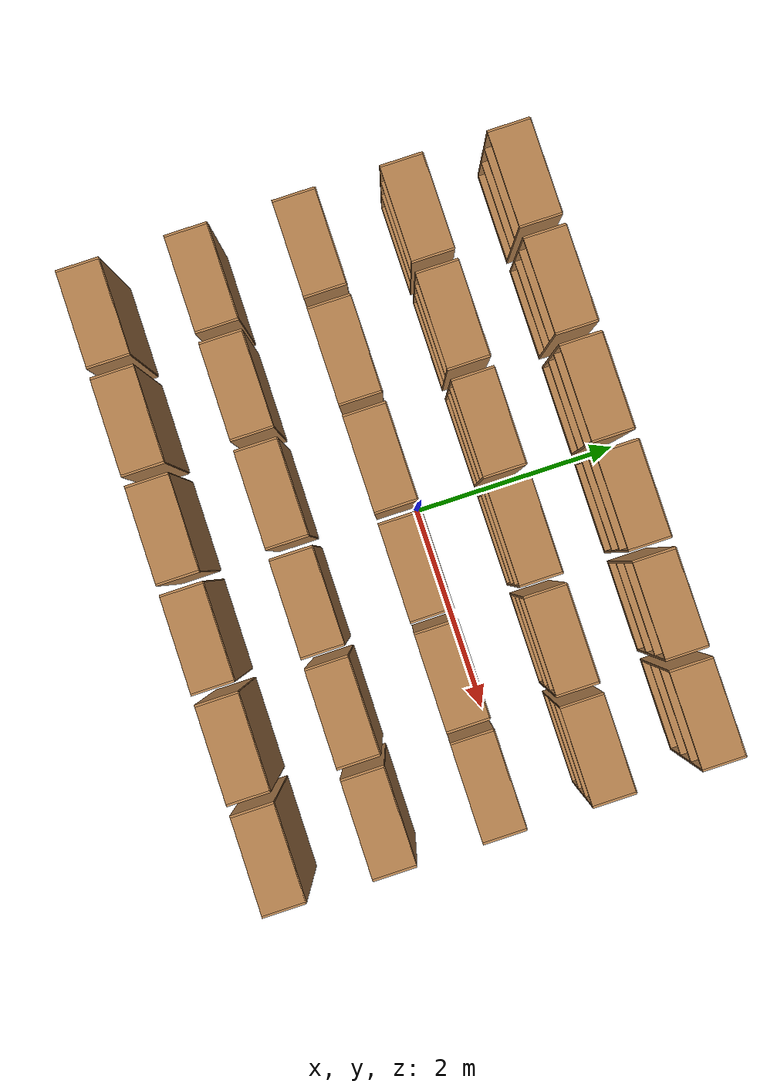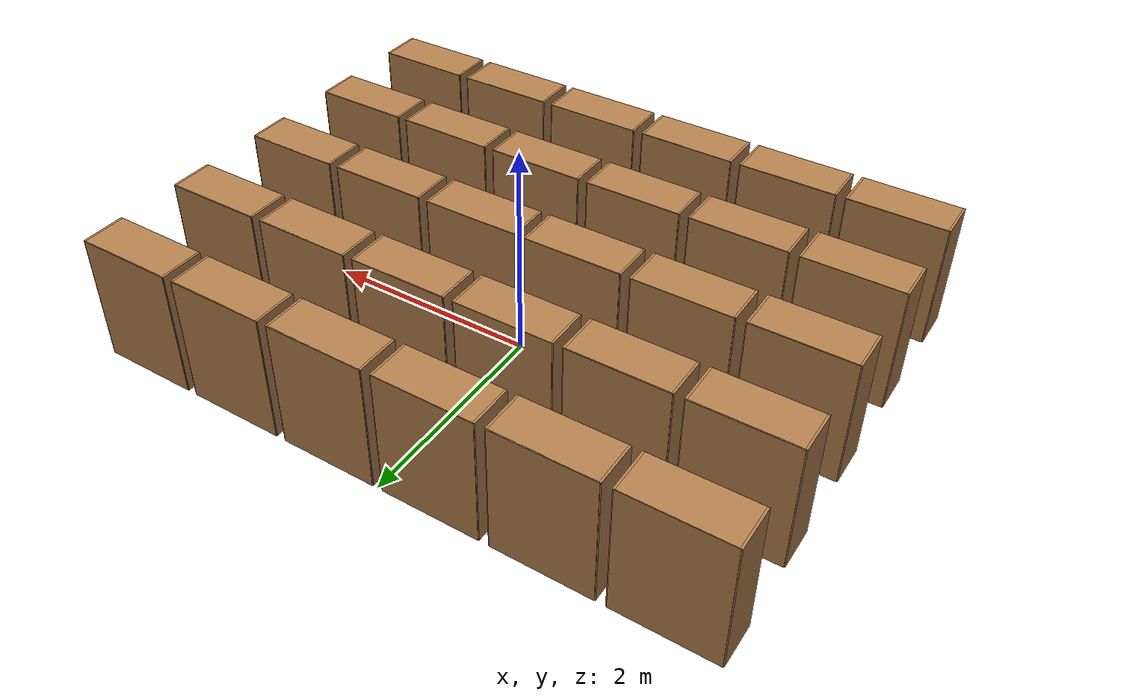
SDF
<?xml version='1.0'?>
<sdf version='1.6'>
  <model name='5Bookshelves'>
    <model name='BookshelfRow'>
      <model name='bookshelf'>
        <static>1</static>
        <link name='link'>
          <inertial>
            <mass>1</mass>
          </inertial>
          <collision name='back'>
            <pose frame=''>0 0.005 0.6 0 -0 0</pose>
            <geometry>
              <box>
                <size>0.9 0.01 1.2</size>
              </box>
            </geometry>
          </collision>
          <visual name='visual1'>
            <pose frame=''>0 0.005 0.6 0 -0 0</pose>
            <geometry>
              <box>
                <size>0.9 0.01 1.2</size>
              </box>
            </geometry>
            <material>
              <script>
                <uri>file://media/materials/scripts/gazebo.material</uri>
                <name>Gazebo/Wood</name>
              </script>
            </material>
          </visual>
          <collision name='left_side'>
            <pose frame=''>0.45 -0.195 0.6 0 -0 0</pose>
            <geometry>
              <box>
                <size>0.02 0.4 1.2</size>
              </box>
            </geometry>
          </collision>
          <visual name='visual2'>
            <pose frame=''>0.45 -0.195 0.6 0 -0 0</pose>
            <geometry>
              <box>
                <size>0.02 0.4 1.2</size>
              </box>
            </geometry>
            <material>
              <script>
                <uri>file://media/materials/scripts/gazebo.material</uri>
                <name>Gazebo/Wood</name>
              </script>
            </material>
          </visual>
          <collision name='right_side'>
            <pose frame=''>-0.45 -0.195 0.6 0 -0 0</pose>
            <geometry>
              <box>
                <size>0.02 0.4 1.2</size>
              </box>
            </geometry>
          </collision>
          <visual name='visual3'>
            <pose frame=''>-0.45 -0.195 0.6 0 -0 0</pose>
            <geometry>
              <box>
                <size>0.02 0.4 1.2</size>
              </box>
            </geometry>
            <material>
              <script>
                <uri>file://media/materials/scripts/gazebo.material</uri>
                <name>Gazebo/Wood</name>
              </script>
            </material>
          </visual>
          <collision name='bottom'>
            <pose frame=''>0 -0.195 0.03 0 -0 0</pose>
            <geometry>
              <box>
                <size>0.88 0.4 0.06</size>
              </box>
            </geometry>
          </collision>
          <visual name='visual4'>
            <pose frame=''>0 -0.195 0.03 0 -0 0</pose>
            <geometry>
              <box>
                <size>0.88 0.4 0.06</size>
              </box>
            </geometry>
            <material>
              <script>
                <uri>file://media/materials/scripts/gazebo.material</uri>
                <name>Gazebo/Wood</name>
              </script>
            </material>
          </visual>
          <collision name='top'>
            <pose frame=''>0 -0.195 1.19 0 -0 0</pose>
            <geometry>
              <box>
                <size>0.88 0.4 0.02</size>
              </box>
            </geometry>
          </collision>
          <visual name='visual5'>
            <pose frame=''>0 -0.195 1.19 0 -0 0</pose>
            <geometry>
              <box>
                <size>0.88 0.4 0.02</size>
              </box>
            </geometry>
            <material>
              <script>
                <uri>file://media/materials/scripts/gazebo.material</uri>
                <name>Gazebo/Wood</name>
              </script>
            </material>
          </visual>
          <collision name='low_shelf'>
            <pose frame=''>0 -0.195 0.43 0 -0 0</pose>
            <geometry>
              <box>
                <size>0.88 0.4 0.02</size>
              </box>
            </geometry>
          </collision>
          <visual name='visual6'>
            <pose frame=''>0 -0.195 0.43 0 -0 0</pose>
            <geometry>
              <box>
                <size>0.88 0.4 0.02</size>
              </box>
            </geometry>
            <material>
              <script>
                <uri>file://media/materials/scripts/gazebo.material</uri>
                <name>Gazebo/Wood</name>
              </script>
            </material>
          </visual>
          <collision name='high_shelf'>
            <pose frame=''>0 -0.195 0.8 0 -0 0</pose>
            <geometry>
              <box>
                <size>0.88 0.4 0.02</size>
              </box>
            </geometry>
          </collision>
          <visual name='visual7'>
            <pose frame=''>0 -0.195 0.8 0 -0 0</pose>
            <geometry>
              <box>
                <size>0.88 0.4 0.02</size>
              </box>
            </geometry>
            <material>
              <script>
                <uri>file://media/materials/scripts/gazebo.material</uri>
                <name>Gazebo/Wood</name>
              </script>
            </material>
          </visual>
        </link>
        <pose frame=''>-2.5 0 0 0 -0 0</pose>
      </model>
      <model name='bookshelf_0'>
        <static>1</static>
        <link name='link'>
          <inertial>
            <mass>1</mass>
          </inertial>
          <collision name='back'>
            <pose frame=''>0 0.005 0.6 0 -0 0</pose>
            <geometry>
              <box>
                <size>0.9 0.01 1.2</size>
              </box>
            </geometry>
          </collision>
          <visual name='visual1'>
            <pose frame=''>0 0.005 0.6 0 -0 0</pose>
            <geometry>
              <box>
                <size>0.9 0.01 1.2</size>
              </box>
            </geometry>
            <material>
              <script>
                <uri>file://media/materials/scripts/gazebo.material</uri>
                <name>Gazebo/Wood</name>
              </script>
            </material>
          </visual>
          <collision name='left_side'>
            <pose frame=''>0.45 -0.195 0.6 0 -0 0</pose>
            <geometry>
              <box>
                <size>0.02 0.4 1.2</size>
              </box>
            </geometry>
          </collision>
          <visual name='visual2'>
            <pose frame=''>0.45 -0.195 0.6 0 -0 0</pose>
            <geometry>
              <box>
                <size>0.02 0.4 1.2</size>
              </box>
            </geometry>
            <material>
              <script>
                <uri>file://media/materials/scripts/gazebo.material</uri>
                <name>Gazebo/Wood</name>
              </script>
            </material>
          </visual>
          <collision name='right_side'>
            <pose frame=''>-0.45 -0.195 0.6 0 -0 0</pose>
            <geometry>
              <box>
                <size>0.02 0.4 1.2</size>
              </box>
            </geometry>
          </collision>
          <visual name='visual3'>
            <pose frame=''>-0.45 -0.195 0.6 0 -0 0</pose>
            <geometry>
              <box>
                <size>0.02 0.4 1.2</size>
              </box>
            </geometry>
            <material>
              <script>
                <uri>file://media/materials/scripts/gazebo.material</uri>
                <name>Gazebo/Wood</name>
              </script>
            </material>
          </visual>
          <collision name='bottom'>
            <pose frame=''>0 -0.195 0.03 0 -0 0</pose>
            <geometry>
              <box>
                <size>0.88 0.4 0.06</size>
              </box>
            </geometry>
          </collision>
          <visual name='visual4'>
            <pose frame=''>0 -0.195 0.03 0 -0 0</pose>
            <geometry>
              <box>
                <size>0.88 0.4 0.06</size>
              </box>
            </geometry>
            <material>
              <script>
                <uri>file://media/materials/scripts/gazebo.material</uri>
                <name>Gazebo/Wood</name>
              </script>
            </material>
          </visual>
          <collision name='top'>
            <pose frame=''>0 -0.195 1.19 0 -0 0</pose>
            <geometry>
              <box>
                <size>0.88 0.4 0.02</size>
              </box>
            </geometry>
          </collision>
          <visual name='visual5'>
            <pose frame=''>0 -0.195 1.19 0 -0 0</pose>
            <geometry>
              <box>
                <size>0.88 0.4 0.02</size>
              </box>
            </geometry>
            <material>
              <script>
                <uri>file://media/materials/scripts/gazebo.material</uri>
                <name>Gazebo/Wood</name>
              </script>
            </material>
          </visual>
          <collision name='low_shelf'>
            <pose frame=''>0 -0.195 0.43 0 -0 0</pose>
            <geometry>
              <box>
                <size>0.88 0.4 0.02</size>
              </box>
            </geometry>
          </collision>
          <visual name='visual6'>
            <pose frame=''>0 -0.195 0.43 0 -0 0</pose>
            <geometry>
              <box>
                <size>0.88 0.4 0.02</size>
              </box>
            </geometry>
            <material>
              <script>
                <uri>file://media/materials/scripts/gazebo.material</uri>
                <name>Gazebo/Wood</name>
              </script>
            </material>
          </visual>
          <collision name='high_shelf'>
            <pose frame=''>0 -0.195 0.8 0 -0 0</pose>
            <geometry>
              <box>
                <size>0.88 0.4 0.02</size>
              </box>
            </geometry>
          </collision>
          <visual name='visual7'>
            <pose frame=''>0 -0.195 0.8 0 -0 0</pose>
            <geometry>
              <box>
                <size>0.88 0.4 0.02</size>
              </box>
            </geometry>
            <material>
              <script>
                <uri>file://media/materials/scripts/gazebo.material</uri>
                <name>Gazebo/Wood</name>
              </script>
            </material>
          </visual>
        </link>
        <pose frame=''>-1.5 0 0 0 -0 0</pose>
      </model>
      <model name='bookshelf_1'>
        <static>1</static>
        <link name='link'>
          <inertial>
            <mass>1</mass>
          </inertial>
          <collision name='back'>
            <pose frame=''>0 0.005 0.6 0 -0 0</pose>
            <geometry>
              <box>
                <size>0.9 0.01 1.2</size>
              </box>
            </geometry>
          </collision>
          <visual name='visual1'>
            <pose frame=''>0 0.005 0.6 0 -0 0</pose>
            <geometry>
              <box>
                <size>0.9 0.01 1.2</size>
              </box>
            </geometry>
            <material>
              <script>
                <uri>file://media/materials/scripts/gazebo.material</uri>
                <name>Gazebo/Wood</name>
              </script>
            </material>
          </visual>
          <collision name='left_side'>
            <pose frame=''>0.45 -0.195 0.6 0 -0 0</pose>
            <geometry>
              <box>
                <size>0.02 0.4 1.2</size>
              </box>
            </geometry>
          </collision>
          <visual name='visual2'>
            <pose frame=''>0.45 -0.195 0.6 0 -0 0</pose>
            <geometry>
              <box>
                <size>0.02 0.4 1.2</size>
              </box>
            </geometry>
            <material>
              <script>
                <uri>file://media/materials/scripts/gazebo.material</uri>
                <name>Gazebo/Wood</name>
              </script>
            </material>
          </visual>
          <collision name='right_side'>
            <pose frame=''>-0.45 -0.195 0.6 0 -0 0</pose>
            <geometry>
              <box>
                <size>0.02 0.4 1.2</size>
              </box>
            </geometry>
          </collision>
          <visual name='visual3'>
            <pose frame=''>-0.45 -0.195 0.6 0 -0 0</pose>
            <geometry>
              <box>
                <size>0.02 0.4 1.2</size>
              </box>
            </geometry>
            <material>
              <script>
                <uri>file://media/materials/scripts/gazebo.material</uri>
                <name>Gazebo/Wood</name>
              </script>
            </material>
          </visual>
          <collision name='bottom'>
            <pose frame=''>0 -0.195 0.03 0 -0 0</pose>
            <geometry>
              <box>
                <size>0.88 0.4 0.06</size>
              </box>
            </geometry>
          </collision>
          <visual name='visual4'>
            <pose frame=''>0 -0.195 0.03 0 -0 0</pose>
            <geometry>
              <box>
                <size>0.88 0.4 0.06</size>
              </box>
            </geometry>
            <material>
              <script>
                <uri>file://media/materials/scripts/gazebo.material</uri>
                <name>Gazebo/Wood</name>
              </script>
            </material>
          </visual>
          <collision name='top'>
            <pose frame=''>0 -0.195 1.19 0 -0 0</pose>
            <geometry>
              <box>
                <size>0.88 0.4 0.02</size>
              </box>
            </geometry>
          </collision>
          <visual name='visual5'>
            <pose frame=''>0 -0.195 1.19 0 -0 0</pose>
            <geometry>
              <box>
                <size>0.88 0.4 0.02</size>
              </box>
            </geometry>
            <material>
              <script>
                <uri>file://media/materials/scripts/gazebo.material</uri>
                <name>Gazebo/Wood</name>
              </script>
            </material>
          </visual>
          <collision name='low_shelf'>
            <pose frame=''>0 -0.195 0.43 0 -0 0</pose>
            <geometry>
              <box>
                <size>0.88 0.4 0.02</size>
              </box>
            </geometry>
          </collision>
          <visual name='visual6'>
            <pose frame=''>0 -0.195 0.43 0 -0 0</pose>
            <geometry>
              <box>
                <size>0.88 0.4 0.02</size>
              </box>
            </geometry>
            <material>
              <script>
                <uri>file://media/materials/scripts/gazebo.material</uri>
                <name>Gazebo/Wood</name>
              </script>
            </material>
          </visual>
          <collision name='high_shelf'>
            <pose frame=''>0 -0.195 0.8 0 -0 0</pose>
            <geometry>
              <box>
                <size>0.88 0.4 0.02</size>
              </box>
            </geometry>
          </collision>
          <visual name='visual7'>
            <pose frame=''>0 -0.195 0.8 0 -0 0</pose>
            <geometry>
              <box>
                <size>0.88 0.4 0.02</size>
              </box>
            </geometry>
            <material>
              <script>
                <uri>file://media/materials/scripts/gazebo.material</uri>
                <name>Gazebo/Wood</name>
              </script>
            </material>
          </visual>
        </link>
        <pose frame=''>-0.5 0 0 0 -0 0</pose>
      </model>
      <model name='bookshelf_2'>
        <static>1</static>
        <link name='link'>
          <inertial>
            <mass>1</mass>
          </inertial>
          <collision name='back'>
            <pose frame=''>0 0.005 0.6 0 -0 0</pose>
            <geometry>
              <box>
                <size>0.9 0.01 1.2</size>
              </box>
            </geometry>
          </collision>
          <visual name='visual1'>
            <pose frame=''>0 0.005 0.6 0 -0 0</pose>
            <geometry>
              <box>
                <size>0.9 0.01 1.2</size>
              </box>
            </geometry>
            <material>
              <script>
                <uri>file://media/materials/scripts/gazebo.material</uri>
                <name>Gazebo/Wood</name>
              </script>
            </material>
          </visual>
          <collision name='left_side'>
            <pose frame=''>0.45 -0.195 0.6 0 -0 0</pose>
            <geometry>
              <box>
                <size>0.02 0.4 1.2</size>
              </box>
            </geometry>
          </collision>
          <visual name='visual2'>
            <pose frame=''>0.45 -0.195 0.6 0 -0 0</pose>
            <geometry>
              <box>
                <size>0.02 0.4 1.2</size>
              </box>
            </geometry>
            <material>
              <script>
                <uri>file://media/materials/scripts/gazebo.material</uri>
                <name>Gazebo/Wood</name>
              </script>
            </material>
          </visual>
          <collision name='right_side'>
            <pose frame=''>-0.45 -0.195 0.6 0 -0 0</pose>
            <geometry>
              <box>
                <size>0.02 0.4 1.2</size>
              </box>
            </geometry>
          </collision>
          <visual name='visual3'>
            <pose frame=''>-0.45 -0.195 0.6 0 -0 0</pose>
            <geometry>
              <box>
                <size>0.02 0.4 1.2</size>
              </box>
            </geometry>
            <material>
              <script>
                <uri>file://media/materials/scripts/gazebo.material</uri>
                <name>Gazebo/Wood</name>
              </script>
            </material>
          </visual>
          <collision name='bottom'>
            <pose frame=''>0 -0.195 0.03 0 -0 0</pose>
            <geometry>
              <box>
                <size>0.88 0.4 0.06</size>
              </box>
            </geometry>
          </collision>
          <visual name='visual4'>
            <pose frame=''>0 -0.195 0.03 0 -0 0</pose>
            <geometry>
              <box>
                <size>0.88 0.4 0.06</size>
              </box>
            </geometry>
            <material>
              <script>
                <uri>file://media/materials/scripts/gazebo.material</uri>
                <name>Gazebo/Wood</name>
              </script>
            </material>
          </visual>
          <collision name='top'>
            <pose frame=''>0 -0.195 1.19 0 -0 0</pose>
            <geometry>
              <box>
                <size>0.88 0.4 0.02</size>
              </box>
            </geometry>
          </collision>
          <visual name='visual5'>
            <pose frame=''>0 -0.195 1.19 0 -0 0</pose>
            <geometry>
              <box>
                <size>0.88 0.4 0.02</size>
              </box>
            </geometry>
            <material>
              <script>
                <uri>file://media/materials/scripts/gazebo.material</uri>
                <name>Gazebo/Wood</name>
              </script>
            </material>
          </visual>
          <collision name='low_shelf'>
            <pose frame=''>0 -0.195 0.43 0 -0 0</pose>
            <geometry>
              <box>
                <size>0.88 0.4 0.02</size>
              </box>
            </geometry>
          </collision>
          <visual name='visual6'>
            <pose frame=''>0 -0.195 0.43 0 -0 0</pose>
            <geometry>
              <box>
                <size>0.88 0.4 0.02</size>
              </box>
            </geometry>
            <material>
              <script>
                <uri>file://media/materials/scripts/gazebo.material</uri>
                <name>Gazebo/Wood</name>
              </script>
            </material>
          </visual>
          <collision name='high_shelf'>
            <pose frame=''>0 -0.195 0.8 0 -0 0</pose>
            <geometry>
              <box>
                <size>0.88 0.4 0.02</size>
              </box>
            </geometry>
          </collision>
          <visual name='visual7'>
            <pose frame=''>0 -0.195 0.8 0 -0 0</pose>
            <geometry>
              <box>
                <size>0.88 0.4 0.02</size>
              </box>
            </geometry>
            <material>
              <script>
                <uri>file://media/materials/scripts/gazebo.material</uri>
                <name>Gazebo/Wood</name>
              </script>
            </material>
          </visual>
        </link>
        <pose frame=''>0.5 0 0 0 -0 0</pose>
      </model>
      <model name='bookshelf_3'>
        <static>1</static>
        <link name='link'>
          <inertial>
            <mass>1</mass>
          </inertial>
          <collision name='back'>
            <pose frame=''>0 0.005 0.6 0 -0 0</pose>
            <geometry>
              <box>
                <size>0.9 0.01 1.2</size>
              </box>
            </geometry>
          </collision>
          <visual name='visual1'>
            <pose frame=''>0 0.005 0.6 0 -0 0</pose>
            <geometry>
              <box>
                <size>0.9 0.01 1.2</size>
              </box>
            </geometry>
            <material>
              <script>
                <uri>file://media/materials/scripts/gazebo.material</uri>
                <name>Gazebo/Wood</name>
              </script>
            </material>
          </visual>
          <collision name='left_side'>
            <pose frame=''>0.45 -0.195 0.6 0 -0 0</pose>
            <geometry>
              <box>
                <size>0.02 0.4 1.2</size>
              </box>
            </geometry>
          </collision>
          <visual name='visual2'>
            <pose frame=''>0.45 -0.195 0.6 0 -0 0</pose>
            <geometry>
              <box>
                <size>0.02 0.4 1.2</size>
              </box>
            </geometry>
            <material>
              <script>
                <uri>file://media/materials/scripts/gazebo.material</uri>
                <name>Gazebo/Wood</name>
              </script>
            </material>
          </visual>
          <collision name='right_side'>
            <pose frame=''>-0.45 -0.195 0.6 0 -0 0</pose>
            <geometry>
              <box>
                <size>0.02 0.4 1.2</size>
              </box>
            </geometry>
          </collision>
          <visual name='visual3'>
            <pose frame=''>-0.45 -0.195 0.6 0 -0 0</pose>
            <geometry>
              <box>
                <size>0.02 0.4 1.2</size>
              </box>
            </geometry>
            <material>
              <script>
                <uri>file://media/materials/scripts/gazebo.material</uri>
                <name>Gazebo/Wood</name>
              </script>
            </material>
          </visual>
          <collision name='bottom'>
            <pose frame=''>0 -0.195 0.03 0 -0 0</pose>
            <geometry>
              <box>
                <size>0.88 0.4 0.06</size>
              </box>
            </geometry>
          </collision>
          <visual name='visual4'>
            <pose frame=''>0 -0.195 0.03 0 -0 0</pose>
            <geometry>
              <box>
                <size>0.88 0.4 0.06</size>
              </box>
            </geometry>
            <material>
              <script>
                <uri>file://media/materials/scripts/gazebo.material</uri>
                <name>Gazebo/Wood</name>
              </script>
            </material>
          </visual>
          <collision name='top'>
            <pose frame=''>0 -0.195 1.19 0 -0 0</pose>
            <geometry>
              <box>
                <size>0.88 0.4 0.02</size>
              </box>
            </geometry>
          </collision>
          <visual name='visual5'>
            <pose frame=''>0 -0.195 1.19 0 -0 0</pose>
            <geometry>
              <box>
                <size>0.88 0.4 0.02</size>
              </box>
            </geometry>
            <material>
              <script>
                <uri>file://media/materials/scripts/gazebo.material</uri>
                <name>Gazebo/Wood</name>
              </script>
            </material>
          </visual>
          <collision name='low_shelf'>
            <pose frame=''>0 -0.195 0.43 0 -0 0</pose>
            <geometry>
              <box>
                <size>0.88 0.4 0.02</size>
              </box>
            </geometry>
          </collision>
          <visual name='visual6'>
            <pose frame=''>0 -0.195 0.43 0 -0 0</pose>
            <geometry>
              <box>
                <size>0.88 0.4 0.02</size>
              </box>
            </geometry>
            <material>
              <script>
                <uri>file://media/materials/scripts/gazebo.material</uri>
                <name>Gazebo/Wood</name>
              </script>
            </material>
          </visual>
          <collision name='high_shelf'>
            <pose frame=''>0 -0.195 0.8 0 -0 0</pose>
            <geometry>
              <box>
                <size>0.88 0.4 0.02</size>
              </box>
            </geometry>
          </collision>
          <visual name='visual7'>
            <pose frame=''>0 -0.195 0.8 0 -0 0</pose>
            <geometry>
              <box>
                <size>0.88 0.4 0.02</size>
              </box>
            </geometry>
            <material>
              <script>
                <uri>file://media/materials/scripts/gazebo.material</uri>
                <name>Gazebo/Wood</name>
              </script>
            </material>
          </visual>
        </link>
        <pose frame=''>1.5 0 0 0 -0 0</pose>
      </model>
      <model name='bookshelf_4'>
        <static>1</static>
        <link name='link'>
          <inertial>
            <mass>1</mass>
          </inertial>
          <collision name='back'>
            <pose frame=''>0 0.005 0.6 0 -0 0</pose>
            <geometry>
              <box>
                <size>0.9 0.01 1.2</size>
              </box>
            </geometry>
          </collision>
          <visual name='visual1'>
            <pose frame=''>0 0.005 0.6 0 -0 0</pose>
            <geometry>
              <box>
                <size>0.9 0.01 1.2</size>
              </box>
            </geometry>
            <material>
              <script>
                <uri>file://media/materials/scripts/gazebo.material</uri>
                <name>Gazebo/Wood</name>
              </script>
            </material>
          </visual>
          <collision name='left_side'>
            <pose frame=''>0.45 -0.195 0.6 0 -0 0</pose>
            <geometry>
              <box>
                <size>0.02 0.4 1.2</size>
              </box>
            </geometry>
          </collision>
          <visual name='visual2'>
            <pose frame=''>0.45 -0.195 0.6 0 -0 0</pose>
            <geometry>
              <box>
                <size>0.02 0.4 1.2</size>
              </box>
            </geometry>
            <material>
              <script>
                <uri>file://media/materials/scripts/gazebo.material</uri>
                <name>Gazebo/Wood</name>
              </script>
            </material>
          </visual>
          <collision name='right_side'>
            <pose frame=''>-0.45 -0.195 0.6 0 -0 0</pose>
            <geometry>
              <box>
                <size>0.02 0.4 1.2</size>
              </box>
            </geometry>
          </collision>
          <visual name='visual3'>
            <pose frame=''>-0.45 -0.195 0.6 0 -0 0</pose>
            <geometry>
              <box>
                <size>0.02 0.4 1.2</size>
              </box>
            </geometry>
            <material>
              <script>
                <uri>file://media/materials/scripts/gazebo.material</uri>
                <name>Gazebo/Wood</name>
              </script>
            </material>
          </visual>
          <collision name='bottom'>
            <pose frame=''>0 -0.195 0.03 0 -0 0</pose>
            <geometry>
              <box>
                <size>0.88 0.4 0.06</size>
              </box>
            </geometry>
          </collision>
          <visual name='visual4'>
            <pose frame=''>0 -0.195 0.03 0 -0 0</pose>
            <geometry>
              <box>
                <size>0.88 0.4 0.06</size>
              </box>
            </geometry>
            <material>
              <script>
                <uri>file://media/materials/scripts/gazebo.material</uri>
                <name>Gazebo/Wood</name>
              </script>
            </material>
          </visual>
          <collision name='top'>
            <pose frame=''>0 -0.195 1.19 0 -0 0</pose>
            <geometry>
              <box>
                <size>0.88 0.4 0.02</size>
              </box>
            </geometry>
          </collision>
          <visual name='visual5'>
            <pose frame=''>0 -0.195 1.19 0 -0 0</pose>
            <geometry>
              <box>
                <size>0.88 0.4 0.02</size>
              </box>
            </geometry>
            <material>
              <script>
                <uri>file://media/materials/scripts/gazebo.material</uri>
                <name>Gazebo/Wood</name>
              </script>
            </material>
          </visual>
          <collision name='low_shelf'>
            <pose frame=''>0 -0.195 0.43 0 -0 0</pose>
            <geometry>
              <box>
                <size>0.88 0.4 0.02</size>
              </box>
            </geometry>
          </collision>
          <visual name='visual6'>
            <pose frame=''>0 -0.195 0.43 0 -0 0</pose>
            <geometry>
              <box>
                <size>0.88 0.4 0.02</size>
              </box>
            </geometry>
            <material>
              <script>
                <uri>file://media/materials/scripts/gazebo.material</uri>
                <name>Gazebo/Wood</name>
              </script>
            </material>
          </visual>
          <collision name='high_shelf'>
            <pose frame=''>0 -0.195 0.8 0 -0 0</pose>
            <geometry>
              <box>
                <size>0.88 0.4 0.02</size>
              </box>
            </geometry>
          </collision>
          <visual name='visual7'>
            <pose frame=''>0 -0.195 0.8 0 -0 0</pose>
            <geometry>
              <box>
                <size>0.88 0.4 0.02</size>
              </box>
            </geometry>
            <material>
              <script>
                <uri>file://media/materials/scripts/gazebo.material</uri>
                <name>Gazebo/Wood</name>
              </script>
            </material>
          </visual>
        </link>
        <pose frame=''>2.5 0 0 0 -0 0</pose>
      </model>
      <static>0</static>
      <allow_auto_disable>1</allow_auto_disable>
      <pose frame=''>0 -2 0 0 -0 0</pose>
    </model>
    <model name='BookshelfRow_0'>
      <model name='bookshelf'>
        <static>1</static>
        <link name='link'>
          <inertial>
            <mass>1</mass>
          </inertial>
          <collision name='back'>
            <pose frame=''>0 0.005 0.6 0 -0 0</pose>
            <geometry>
              <box>
                <size>0.9 0.01 1.2</size>
              </box>
            </geometry>
          </collision>
          <visual name='visual1'>
            <pose frame=''>0 0.005 0.6 0 -0 0</pose>
            <geometry>
              <box>
                <size>0.9 0.01 1.2</size>
              </box>
            </geometry>
            <material>
              <script>
                <uri>file://media/materials/scripts/gazebo.material</uri>
                <name>Gazebo/Wood</name>
              </script>
            </material>
          </visual>
          <collision name='left_side'>
            <pose frame=''>0.45 -0.195 0.6 0 -0 0</pose>
            <geometry>
              <box>
                <size>0.02 0.4 1.2</size>
              </box>
            </geometry>
          </collision>
          <visual name='visual2'>
            <pose frame=''>0.45 -0.195 0.6 0 -0 0</pose>
            <geometry>
              <box>
                <size>0.02 0.4 1.2</size>
              </box>
            </geometry>
            <material>
              <script>
                <uri>file://media/materials/scripts/gazebo.material</uri>
                <name>Gazebo/Wood</name>
              </script>
            </material>
          </visual>
          <collision name='right_side'>
            <pose frame=''>-0.45 -0.195 0.6 0 -0 0</pose>
            <geometry>
              <box>
                <size>0.02 0.4 1.2</size>
              </box>
            </geometry>
          </collision>
          <visual name='visual3'>
            <pose frame=''>-0.45 -0.195 0.6 0 -0 0</pose>
            <geometry>
              <box>
                <size>0.02 0.4 1.2</size>
              </box>
            </geometry>
            <material>
              <script>
                <uri>file://media/materials/scripts/gazebo.material</uri>
                <name>Gazebo/Wood</name>
              </script>
            </material>
          </visual>
          <collision name='bottom'>
            <pose frame=''>0 -0.195 0.03 0 -0 0</pose>
            <geometry>
              <box>
                <size>0.88 0.4 0.06</size>
              </box>
            </geometry>
          </collision>
          <visual name='visual4'>
            <pose frame=''>0 -0.195 0.03 0 -0 0</pose>
            <geometry>
              <box>
                <size>0.88 0.4 0.06</size>
              </box>
            </geometry>
            <material>
              <script>
                <uri>file://media/materials/scripts/gazebo.material</uri>
                <name>Gazebo/Wood</name>
              </script>
            </material>
          </visual>
          <collision name='top'>
            <pose frame=''>0 -0.195 1.19 0 -0 0</pose>
            <geometry>
              <box>
                <size>0.88 0.4 0.02</size>
              </box>
            </geometry>
          </collision>
          <visual name='visual5'>
            <pose frame=''>0 -0.195 1.19 0 -0 0</pose>
            <geometry>
              <box>
                <size>0.88 0.4 0.02</size>
              </box>
            </geometry>
            <material>
              <script>
                <uri>file://media/materials/scripts/gazebo.material</uri>
                <name>Gazebo/Wood</name>
              </script>
            </material>
          </visual>
          <collision name='low_shelf'>
            <pose frame=''>0 -0.195 0.43 0 -0 0</pose>
            <geometry>
              <box>
                <size>0.88 0.4 0.02</size>
              </box>
            </geometry>
          </collision>
          <visual name='visual6'>
            <pose frame=''>0 -0.195 0.43 0 -0 0</pose>
            <geometry>
              <box>
                <size>0.88 0.4 0.02</size>
              </box>
            </geometry>
            <material>
              <script>
                <uri>file://media/materials/scripts/gazebo.material</uri>
                <name>Gazebo/Wood</name>
              </script>
            </material>
          </visual>
          <collision name='high_shelf'>
            <pose frame=''>0 -0.195 0.8 0 -0 0</pose>
            <geometry>
              <box>
                <size>0.88 0.4 0.02</size>
              </box>
            </geometry>
          </collision>
          <visual name='visual7'>
            <pose frame=''>0 -0.195 0.8 0 -0 0</pose>
            <geometry>
              <box>
                <size>0.88 0.4 0.02</size>
              </box>
            </geometry>
            <material>
              <script>
                <uri>file://media/materials/scripts/gazebo.material</uri>
                <name>Gazebo/Wood</name>
              </script>
            </material>
          </visual>
        </link>
        <pose frame=''>-2.5 0 0 0 -0 0</pose>
      </model>
      <model name='bookshelf_0'>
        <static>1</static>
        <link name='link'>
          <inertial>
            <mass>1</mass>
          </inertial>
          <collision name='back'>
            <pose frame=''>0 0.005 0.6 0 -0 0</pose>
            <geometry>
              <box>
                <size>0.9 0.01 1.2</size>
              </box>
            </geometry>
          </collision>
          <visual name='visual1'>
            <pose frame=''>0 0.005 0.6 0 -0 0</pose>
            <geometry>
              <box>
                <size>0.9 0.01 1.2</size>
              </box>
            </geometry>
            <material>
              <script>
                <uri>file://media/materials/scripts/gazebo.material</uri>
                <name>Gazebo/Wood</name>
              </script>
            </material>
          </visual>
          <collision name='left_side'>
            <pose frame=''>0.45 -0.195 0.6 0 -0 0</pose>
            <geometry>
              <box>
                <size>0.02 0.4 1.2</size>
              </box>
            </geometry>
          </collision>
          <visual name='visual2'>
            <pose frame=''>0.45 -0.195 0.6 0 -0 0</pose>
            <geometry>
              <box>
                <size>0.02 0.4 1.2</size>
              </box>
            </geometry>
            <material>
              <script>
                <uri>file://media/materials/scripts/gazebo.material</uri>
                <name>Gazebo/Wood</name>
              </script>
            </material>
          </visual>
          <collision name='right_side'>
            <pose frame=''>-0.45 -0.195 0.6 0 -0 0</pose>
            <geometry>
              <box>
                <size>0.02 0.4 1.2</size>
              </box>
            </geometry>
          </collision>
          <visual name='visual3'>
            <pose frame=''>-0.45 -0.195 0.6 0 -0 0</pose>
            <geometry>
              <box>
                <size>0.02 0.4 1.2</size>
              </box>
            </geometry>
            <material>
              <script>
                <uri>file://media/materials/scripts/gazebo.material</uri>
                <name>Gazebo/Wood</name>
              </script>
            </material>
          </visual>
          <collision name='bottom'>
            <pose frame=''>0 -0.195 0.03 0 -0 0</pose>
            <geometry>
              <box>
                <size>0.88 0.4 0.06</size>
              </box>
            </geometry>
          </collision>
          <visual name='visual4'>
            <pose frame=''>0 -0.195 0.03 0 -0 0</pose>
            <geometry>
              <box>
                <size>0.88 0.4 0.06</size>
              </box>
            </geometry>
            <material>
              <script>
                <uri>file://media/materials/scripts/gazebo.material</uri>
                <name>Gazebo/Wood</name>
              </script>
            </material>
          </visual>
          <collision name='top'>
            <pose frame=''>0 -0.195 1.19 0 -0 0</pose>
            <geometry>
              <box>
                <size>0.88 0.4 0.02</size>
              </box>
            </geometry>
          </collision>
          <visual name='visual5'>
            <pose frame=''>0 -0.195 1.19 0 -0 0</pose>
            <geometry>
              <box>
                <size>0.88 0.4 0.02</size>
              </box>
            </geometry>
            <material>
              <script>
                <uri>file://media/materials/scripts/gazebo.material</uri>
                <name>Gazebo/Wood</name>
              </script>
            </material>
          </visual>
          <collision name='low_shelf'>
            <pose frame=''>0 -0.195 0.43 0 -0 0</pose>
            <geometry>
              <box>
                <size>0.88 0.4 0.02</size>
              </box>
            </geometry>
          </collision>
          <visual name='visual6'>
            <pose frame=''>0 -0.195 0.43 0 -0 0</pose>
            <geometry>
              <box>
                <size>0.88 0.4 0.02</size>
              </box>
            </geometry>
            <material>
              <script>
                <uri>file://media/materials/scripts/gazebo.material</uri>
                <name>Gazebo/Wood</name>
              </script>
            </material>
          </visual>
          <collision name='high_shelf'>
            <pose frame=''>0 -0.195 0.8 0 -0 0</pose>
            <geometry>
              <box>
                <size>0.88 0.4 0.02</size>
              </box>
            </geometry>
          </collision>
          <visual name='visual7'>
            <pose frame=''>0 -0.195 0.8 0 -0 0</pose>
            <geometry>
              <box>
                <size>0.88 0.4 0.02</size>
              </box>
            </geometry>
            <material>
              <script>
                <uri>file://media/materials/scripts/gazebo.material</uri>
                <name>Gazebo/Wood</name>
              </script>
            </material>
          </visual>
        </link>
        <pose frame=''>-1.5 0 0 0 -0 0</pose>
      </model>
      <model name='bookshelf_1'>
        <static>1</static>
        <link name='link'>
          <inertial>
            <mass>1</mass>
          </inertial>
          <collision name='back'>
            <pose frame=''>0 0.005 0.6 0 -0 0</pose>
            <geometry>
              <box>
                <size>0.9 0.01 1.2</size>
              </box>
            </geometry>
          </collision>
          <visual name='visual1'>
            <pose frame=''>0 0.005 0.6 0 -0 0</pose>
            <geometry>
              <box>
                <size>0.9 0.01 1.2</size>
              </box>
            </geometry>
            <material>
              <script>
                <uri>file://media/materials/scripts/gazebo.material</uri>
                <name>Gazebo/Wood</name>
              </script>
            </material>
          </visual>
          <collision name='left_side'>
            <pose frame=''>0.45 -0.195 0.6 0 -0 0</pose>
            <geometry>
              <box>
                <size>0.02 0.4 1.2</size>
              </box>
            </geometry>
          </collision>
          <visual name='visual2'>
            <pose frame=''>0.45 -0.195 0.6 0 -0 0</pose>
            <geometry>
              <box>
                <size>0.02 0.4 1.2</size>
              </box>
            </geometry>
            <material>
              <script>
                <uri>file://media/materials/scripts/gazebo.material</uri>
                <name>Gazebo/Wood</name>
              </script>
            </material>
          </visual>
          <collision name='right_side'>
            <pose frame=''>-0.45 -0.195 0.6 0 -0 0</pose>
            <geometry>
              <box>
                <size>0.02 0.4 1.2</size>
              </box>
            </geometry>
          </collision>
          <visual name='visual3'>
            <pose frame=''>-0.45 -0.195 0.6 0 -0 0</pose>
            <geometry>
              <box>
                <size>0.02 0.4 1.2</size>
              </box>
            </geometry>
            <material>
              <script>
                <uri>file://media/materials/scripts/gazebo.material</uri>
                <name>Gazebo/Wood</name>
              </script>
            </material>
          </visual>
          <collision name='bottom'>
            <pose frame=''>0 -0.195 0.03 0 -0 0</pose>
            <geometry>
              <box>
                <size>0.88 0.4 0.06</size>
              </box>
            </geometry>
          </collision>
          <visual name='visual4'>
            <pose frame=''>0 -0.195 0.03 0 -0 0</pose>
            <geometry>
              <box>
                <size>0.88 0.4 0.06</size>
              </box>
            </geometry>
            <material>
              <script>
                <uri>file://media/materials/scripts/gazebo.material</uri>
                <name>Gazebo/Wood</name>
              </script>
            </material>
          </visual>
          <collision name='top'>
            <pose frame=''>0 -0.195 1.19 0 -0 0</pose>
            <geometry>
              <box>
                <size>0.88 0.4 0.02</size>
              </box>
            </geometry>
          </collision>
          <visual name='visual5'>
            <pose frame=''>0 -0.195 1.19 0 -0 0</pose>
            <geometry>
              <box>
                <size>0.88 0.4 0.02</size>
              </box>
            </geometry>
            <material>
              <script>
                <uri>file://media/materials/scripts/gazebo.material</uri>
                <name>Gazebo/Wood</name>
              </script>
            </material>
          </visual>
          <collision name='low_shelf'>
            <pose frame=''>0 -0.195 0.43 0 -0 0</pose>
            <geometry>
              <box>
                <size>0.88 0.4 0.02</size>
              </box>
            </geometry>
          </collision>
          <visual name='visual6'>
            <pose frame=''>0 -0.195 0.43 0 -0 0</pose>
            <geometry>
              <box>
                <size>0.88 0.4 0.02</size>
              </box>
            </geometry>
            <material>
              <script>
                <uri>file://media/materials/scripts/gazebo.material</uri>
                <name>Gazebo/Wood</name>
              </script>
            </material>
          </visual>
          <collision name='high_shelf'>
            <pose frame=''>0 -0.195 0.8 0 -0 0</pose>
            <geometry>
              <box>
                <size>0.88 0.4 0.02</size>
              </box>
            </geometry>
          </collision>
          <visual name='visual7'>
            <pose frame=''>0 -0.195 0.8 0 -0 0</pose>
            <geometry>
              <box>
                <size>0.88 0.4 0.02</size>
              </box>
            </geometry>
            <material>
              <script>
                <uri>file://media/materials/scripts/gazebo.material</uri>
                <name>Gazebo/Wood</name>
              </script>
            </material>
          </visual>
        </link>
        <pose frame=''>-0.5 0 0 0 -0 0</pose>
      </model>
      <model name='bookshelf_2'>
        <static>1</static>
        <link name='link'>
          <inertial>
            <mass>1</mass>
          </inertial>
          <collision name='back'>
            <pose frame=''>0 0.005 0.6 0 -0 0</pose>
            <geometry>
              <box>
                <size>0.9 0.01 1.2</size>
              </box>
            </geometry>
          </collision>
          <visual name='visual1'>
            <pose frame=''>0 0.005 0.6 0 -0 0</pose>
            <geometry>
              <box>
                <size>0.9 0.01 1.2</size>
              </box>
            </geometry>
            <material>
              <script>
                <uri>file://media/materials/scripts/gazebo.material</uri>
                <name>Gazebo/Wood</name>
              </script>
            </material>
          </visual>
          <collision name='left_side'>
            <pose frame=''>0.45 -0.195 0.6 0 -0 0</pose>
            <geometry>
              <box>
                <size>0.02 0.4 1.2</size>
              </box>
            </geometry>
          </collision>
          <visual name='visual2'>
            <pose frame=''>0.45 -0.195 0.6 0 -0 0</pose>
            <geometry>
              <box>
                <size>0.02 0.4 1.2</size>
              </box>
            </geometry>
            <material>
              <script>
                <uri>file://media/materials/scripts/gazebo.material</uri>
                <name>Gazebo/Wood</name>
              </script>
            </material>
          </visual>
          <collision name='right_side'>
            <pose frame=''>-0.45 -0.195 0.6 0 -0 0</pose>
            <geometry>
              <box>
                <size>0.02 0.4 1.2</size>
              </box>
            </geometry>
          </collision>
          <visual name='visual3'>
            <pose frame=''>-0.45 -0.195 0.6 0 -0 0</pose>
            <geometry>
              <box>
                <size>0.02 0.4 1.2</size>
              </box>
            </geometry>
            <material>
              <script>
                <uri>file://media/materials/scripts/gazebo.material</uri>
                <name>Gazebo/Wood</name>
              </script>
            </material>
          </visual>
          <collision name='bottom'>
            <pose frame=''>0 -0.195 0.03 0 -0 0</pose>
            <geometry>
              <box>
                <size>0.88 0.4 0.06</size>
              </box>
            </geometry>
          </collision>
          <visual name='visual4'>
            <pose frame=''>0 -0.195 0.03 0 -0 0</pose>
            <geometry>
              <box>
                <size>0.88 0.4 0.06</size>
              </box>
            </geometry>
            <material>
              <script>
                <uri>file://media/materials/scripts/gazebo.material</uri>
                <name>Gazebo/Wood</name>
              </script>
            </material>
          </visual>
          <collision name='top'>
            <pose frame=''>0 -0.195 1.19 0 -0 0</pose>
            <geometry>
              <box>
                <size>0.88 0.4 0.02</size>
              </box>
            </geometry>
          </collision>
          <visual name='visual5'>
            <pose frame=''>0 -0.195 1.19 0 -0 0</pose>
            <geometry>
              <box>
                <size>0.88 0.4 0.02</size>
              </box>
            </geometry>
            <material>
              <script>
                <uri>file://media/materials/scripts/gazebo.material</uri>
                <name>Gazebo/Wood</name>
              </script>
            </material>
          </visual>
          <collision name='low_shelf'>
            <pose frame=''>0 -0.195 0.43 0 -0 0</pose>
            <geometry>
              <box>
                <size>0.88 0.4 0.02</size>
              </box>
            </geometry>
          </collision>
          <visual name='visual6'>
            <pose frame=''>0 -0.195 0.43 0 -0 0</pose>
            <geometry>
              <box>
                <size>0.88 0.4 0.02</size>
              </box>
            </geometry>
            <material>
              <script>
                <uri>file://media/materials/scripts/gazebo.material</uri>
                <name>Gazebo/Wood</name>
              </script>
            </material>
          </visual>
          <collision name='high_shelf'>
            <pose frame=''>0 -0.195 0.8 0 -0 0</pose>
            <geometry>
              <box>
                <size>0.88 0.4 0.02</size>
              </box>
            </geometry>
          </collision>
          <visual name='visual7'>
            <pose frame=''>0 -0.195 0.8 0 -0 0</pose>
            <geometry>
              <box>
                <size>0.88 0.4 0.02</size>
              </box>
            </geometry>
            <material>
              <script>
                <uri>file://media/materials/scripts/gazebo.material</uri>
                <name>Gazebo/Wood</name>
              </script>
            </material>
          </visual>
        </link>
        <pose frame=''>0.5 0 0 0 -0 0</pose>
      </model>
      <model name='bookshelf_3'>
        <static>1</static>
        <link name='link'>
          <inertial>
            <mass>1</mass>
          </inertial>
          <collision name='back'>
            <pose frame=''>0 0.005 0.6 0 -0 0</pose>
            <geometry>
              <box>
                <size>0.9 0.01 1.2</size>
              </box>
            </geometry>
          </collision>
          <visual name='visual1'>
            <pose frame=''>0 0.005 0.6 0 -0 0</pose>
            <geometry>
              <box>
                <size>0.9 0.01 1.2</size>
              </box>
            </geometry>
            <material>
              <script>
                <uri>file://media/materials/scripts/gazebo.material</uri>
                <name>Gazebo/Wood</name>
              </script>
            </material>
          </visual>
          <collision name='left_side'>
            <pose frame=''>0.45 -0.195 0.6 0 -0 0</pose>
            <geometry>
              <box>
                <size>0.02 0.4 1.2</size>
              </box>
            </geometry>
          </collision>
          <visual name='visual2'>
            <pose frame=''>0.45 -0.195 0.6 0 -0 0</pose>
            <geometry>
              <box>
                <size>0.02 0.4 1.2</size>
              </box>
            </geometry>
            <material>
              <script>
                <uri>file://media/materials/scripts/gazebo.material</uri>
                <name>Gazebo/Wood</name>
              </script>
            </material>
          </visual>
          <collision name='right_side'>
            <pose frame=''>-0.45 -0.195 0.6 0 -0 0</pose>
            <geometry>
              <box>
                <size>0.02 0.4 1.2</size>
              </box>
            </geometry>
          </collision>
          <visual name='visual3'>
            <pose frame=''>-0.45 -0.195 0.6 0 -0 0</pose>
            <geometry>
              <box>
                <size>0.02 0.4 1.2</size>
              </box>
            </geometry>
            <material>
              <script>
                <uri>file://media/materials/scripts/gazebo.material</uri>
                <name>Gazebo/Wood</name>
              </script>
            </material>
          </visual>
          <collision name='bottom'>
            <pose frame=''>0 -0.195 0.03 0 -0 0</pose>
            <geometry>
              <box>
                <size>0.88 0.4 0.06</size>
              </box>
            </geometry>
          </collision>
          <visual name='visual4'>
            <pose frame=''>0 -0.195 0.03 0 -0 0</pose>
            <geometry>
              <box>
                <size>0.88 0.4 0.06</size>
              </box>
            </geometry>
            <material>
              <script>
                <uri>file://media/materials/scripts/gazebo.material</uri>
                <name>Gazebo/Wood</name>
              </script>
            </material>
          </visual>
          <collision name='top'>
            <pose frame=''>0 -0.195 1.19 0 -0 0</pose>
            <geometry>
              <box>
                <size>0.88 0.4 0.02</size>
              </box>
            </geometry>
          </collision>
          <visual name='visual5'>
            <pose frame=''>0 -0.195 1.19 0 -0 0</pose>
            <geometry>
              <box>
                <size>0.88 0.4 0.02</size>
              </box>
            </geometry>
            <material>
              <script>
                <uri>file://media/materials/scripts/gazebo.material</uri>
                <name>Gazebo/Wood</name>
              </script>
            </material>
          </visual>
          <collision name='low_shelf'>
            <pose frame=''>0 -0.195 0.43 0 -0 0</pose>
            <geometry>
              <box>
                <size>0.88 0.4 0.02</size>
              </box>
            </geometry>
          </collision>
          <visual name='visual6'>
            <pose frame=''>0 -0.195 0.43 0 -0 0</pose>
            <geometry>
              <box>
                <size>0.88 0.4 0.02</size>
              </box>
            </geometry>
            <material>
              <script>
                <uri>file://media/materials/scripts/gazebo.material</uri>
                <name>Gazebo/Wood</name>
              </script>
            </material>
          </visual>
          <collision name='high_shelf'>
            <pose frame=''>0 -0.195 0.8 0 -0 0</pose>
            <geometry>
              <box>
                <size>0.88 0.4 0.02</size>
              </box>
            </geometry>
          </collision>
          <visual name='visual7'>
            <pose frame=''>0 -0.195 0.8 0 -0 0</pose>
            <geometry>
              <box>
                <size>0.88 0.4 0.02</size>
              </box>
            </geometry>
            <material>
              <script>
                <uri>file://media/materials/scripts/gazebo.material</uri>
                <name>Gazebo/Wood</name>
              </script>
            </material>
          </visual>
        </link>
        <pose frame=''>1.5 0 0 0 -0 0</pose>
      </model>
      <model name='bookshelf_4'>
        <static>1</static>
        <link name='link'>
          <inertial>
            <mass>1</mass>
          </inertial>
          <collision name='back'>
            <pose frame=''>0 0.005 0.6 0 -0 0</pose>
            <geometry>
              <box>
                <size>0.9 0.01 1.2</size>
              </box>
            </geometry>
          </collision>
          <visual name='visual1'>
            <pose frame=''>0 0.005 0.6 0 -0 0</pose>
            <geometry>
              <box>
                <size>0.9 0.01 1.2</size>
              </box>
            </geometry>
            <material>
              <script>
                <uri>file://media/materials/scripts/gazebo.material</uri>
                <name>Gazebo/Wood</name>
              </script>
            </material>
          </visual>
          <collision name='left_side'>
            <pose frame=''>0.45 -0.195 0.6 0 -0 0</pose>
            <geometry>
              <box>
                <size>0.02 0.4 1.2</size>
              </box>
            </geometry>
          </collision>
          <visual name='visual2'>
            <pose frame=''>0.45 -0.195 0.6 0 -0 0</pose>
            <geometry>
              <box>
                <size>0.02 0.4 1.2</size>
              </box>
            </geometry>
            <material>
              <script>
                <uri>file://media/materials/scripts/gazebo.material</uri>
                <name>Gazebo/Wood</name>
              </script>
            </material>
          </visual>
          <collision name='right_side'>
            <pose frame=''>-0.45 -0.195 0.6 0 -0 0</pose>
            <geometry>
              <box>
                <size>0.02 0.4 1.2</size>
              </box>
            </geometry>
          </collision>
          <visual name='visual3'>
            <pose frame=''>-0.45 -0.195 0.6 0 -0 0</pose>
            <geometry>
              <box>
                <size>0.02 0.4 1.2</size>
              </box>
            </geometry>
            <material>
              <script>
                <uri>file://media/materials/scripts/gazebo.material</uri>
                <name>Gazebo/Wood</name>
              </script>
            </material>
          </visual>
          <collision name='bottom'>
            <pose frame=''>0 -0.195 0.03 0 -0 0</pose>
            <geometry>
              <box>
                <size>0.88 0.4 0.06</size>
              </box>
            </geometry>
          </collision>
          <visual name='visual4'>
            <pose frame=''>0 -0.195 0.03 0 -0 0</pose>
            <geometry>
              <box>
                <size>0.88 0.4 0.06</size>
              </box>
            </geometry>
            <material>
              <script>
                <uri>file://media/materials/scripts/gazebo.material</uri>
                <name>Gazebo/Wood</name>
              </script>
            </material>
          </visual>
          <collision name='top'>
            <pose frame=''>0 -0.195 1.19 0 -0 0</pose>
            <geometry>
              <box>
                <size>0.88 0.4 0.02</size>
              </box>
            </geometry>
          </collision>
          <visual name='visual5'>
            <pose frame=''>0 -0.195 1.19 0 -0 0</pose>
            <geometry>
              <box>
                <size>0.88 0.4 0.02</size>
              </box>
            </geometry>
            <material>
              <script>
                <uri>file://media/materials/scripts/gazebo.material</uri>
                <name>Gazebo/Wood</name>
              </script>
            </material>
          </visual>
          <collision name='low_shelf'>
            <pose frame=''>0 -0.195 0.43 0 -0 0</pose>
            <geometry>
              <box>
                <size>0.88 0.4 0.02</size>
              </box>
            </geometry>
          </collision>
          <visual name='visual6'>
            <pose frame=''>0 -0.195 0.43 0 -0 0</pose>
            <geometry>
              <box>
                <size>0.88 0.4 0.02</size>
              </box>
            </geometry>
            <material>
              <script>
                <uri>file://media/materials/scripts/gazebo.material</uri>
                <name>Gazebo/Wood</name>
              </script>
            </material>
          </visual>
          <collision name='high_shelf'>
            <pose frame=''>0 -0.195 0.8 0 -0 0</pose>
            <geometry>
              <box>
                <size>0.88 0.4 0.02</size>
              </box>
            </geometry>
          </collision>
          <visual name='visual7'>
            <pose frame=''>0 -0.195 0.8 0 -0 0</pose>
            <geometry>
              <box>
                <size>0.88 0.4 0.02</size>
              </box>
            </geometry>
            <material>
              <script>
                <uri>file://media/materials/scripts/gazebo.material</uri>
                <name>Gazebo/Wood</name>
              </script>
            </material>
          </visual>
        </link>
        <pose frame=''>2.5 0 0 0 -0 0</pose>
      </model>
      <static>0</static>
      <allow_auto_disable>1</allow_auto_disable>
      <pose frame=''>0 -1 0 0 -0 0</pose>
    </model>
    <model name='BookshelfRow_1'>
      <model name='bookshelf'>
        <static>1</static>
        <link name='link'>
          <inertial>
            <mass>1</mass>
          </inertial>
          <collision name='back'>
            <pose frame=''>0 0.005 0.6 0 -0 0</pose>
            <geometry>
              <box>
                <size>0.9 0.01 1.2</size>
              </box>
            </geometry>
          </collision>
          <visual name='visual1'>
            <pose frame=''>0 0.005 0.6 0 -0 0</pose>
            <geometry>
              <box>
                <size>0.9 0.01 1.2</size>
              </box>
            </geometry>
            <material>
              <script>
                <uri>file://media/materials/scripts/gazebo.material</uri>
                <name>Gazebo/Wood</name>
              </script>
            </material>
          </visual>
          <collision name='left_side'>
            <pose frame=''>0.45 -0.195 0.6 0 -0 0</pose>
            <geometry>
              <box>
                <size>0.02 0.4 1.2</size>
              </box>
            </geometry>
          </collision>
          <visual name='visual2'>
            <pose frame=''>0.45 -0.195 0.6 0 -0 0</pose>
            <geometry>
              <box>
                <size>0.02 0.4 1.2</size>
              </box>
            </geometry>
            <material>
              <script>
                <uri>file://media/materials/scripts/gazebo.material</uri>
                <name>Gazebo/Wood</name>
              </script>
            </material>
          </visual>
          <collision name='right_side'>
            <pose frame=''>-0.45 -0.195 0.6 0 -0 0</pose>
            <geometry>
              <box>
                <size>0.02 0.4 1.2</size>
              </box>
            </geometry>
          </collision>
          <visual name='visual3'>
            <pose frame=''>-0.45 -0.195 0.6 0 -0 0</pose>
            <geometry>
              <box>
                <size>0.02 0.4 1.2</size>
              </box>
            </geometry>
            <material>
              <script>
                <uri>file://media/materials/scripts/gazebo.material</uri>
                <name>Gazebo/Wood</name>
              </script>
            </material>
          </visual>
          <collision name='bottom'>
            <pose frame=''>0 -0.195 0.03 0 -0 0</pose>
            <geometry>
              <box>
                <size>0.88 0.4 0.06</size>
              </box>
            </geometry>
          </collision>
          <visual name='visual4'>
            <pose frame=''>0 -0.195 0.03 0 -0 0</pose>
            <geometry>
              <box>
                <size>0.88 0.4 0.06</size>
              </box>
            </geometry>
            <material>
              <script>
                <uri>file://media/materials/scripts/gazebo.material</uri>
                <name>Gazebo/Wood</name>
              </script>
            </material>
          </visual>
          <collision name='top'>
            <pose frame=''>0 -0.195 1.19 0 -0 0</pose>
            <geometry>
              <box>
                <size>0.88 0.4 0.02</size>
              </box>
            </geometry>
          </collision>
          <visual name='visual5'>
            <pose frame=''>0 -0.195 1.19 0 -0 0</pose>
            <geometry>
              <box>
                <size>0.88 0.4 0.02</size>
              </box>
            </geometry>
            <material>
              <script>
                <uri>file://media/materials/scripts/gazebo.material</uri>
                <name>Gazebo/Wood</name>
              </script>
            </material>
          </visual>
          <collision name='low_shelf'>
            <pose frame=''>0 -0.195 0.43 0 -0 0</pose>
            <geometry>
              <box>
                <size>0.88 0.4 0.02</size>
              </box>
            </geometry>
          </collision>
          <visual name='visual6'>
            <pose frame=''>0 -0.195 0.43 0 -0 0</pose>
            <geometry>
              <box>
                <size>0.88 0.4 0.02</size>
              </box>
            </geometry>
            <material>
              <script>
                <uri>file://media/materials/scripts/gazebo.material</uri>
                <name>Gazebo/Wood</name>
              </script>
            </material>
          </visual>
          <collision name='high_shelf'>
            <pose frame=''>0 -0.195 0.8 0 -0 0</pose>
            <geometry>
              <box>
                <size>0.88 0.4 0.02</size>
              </box>
            </geometry>
          </collision>
          <visual name='visual7'>
            <pose frame=''>0 -0.195 0.8 0 -0 0</pose>
            <geometry>
              <box>
                <size>0.88 0.4 0.02</size>
              </box>
            </geometry>
            <material>
              <script>
                <uri>file://media/materials/scripts/gazebo.material</uri>
                <name>Gazebo/Wood</name>
              </script>
            </material>
          </visual>
        </link>
        <pose frame=''>-2.5 0 0 0 -0 0</pose>
      </model>
      <model name='bookshelf_0'>
        <static>1</static>
        <link name='link'>
          <inertial>
            <mass>1</mass>
          </inertial>
          <collision name='back'>
            <pose frame=''>0 0.005 0.6 0 -0 0</pose>
            <geometry>
              <box>
                <size>0.9 0.01 1.2</size>
              </box>
            </geometry>
          </collision>
          <visual name='visual1'>
            <pose frame=''>0 0.005 0.6 0 -0 0</pose>
            <geometry>
              <box>
                <size>0.9 0.01 1.2</size>
              </box>
            </geometry>
            <material>
              <script>
                <uri>file://media/materials/scripts/gazebo.material</uri>
                <name>Gazebo/Wood</name>
              </script>
            </material>
          </visual>
          <collision name='left_side'>
            <pose frame=''>0.45 -0.195 0.6 0 -0 0</pose>
            <geometry>
              <box>
                <size>0.02 0.4 1.2</size>
              </box>
            </geometry>
          </collision>
          <visual name='visual2'>
            <pose frame=''>0.45 -0.195 0.6 0 -0 0</pose>
            <geometry>
              <box>
                <size>0.02 0.4 1.2</size>
              </box>
            </geometry>
            <material>
              <script>
                <uri>file://media/materials/scripts/gazebo.material</uri>
                <name>Gazebo/Wood</name>
              </script>
            </material>
          </visual>
          <collision name='right_side'>
            <pose frame=''>-0.45 -0.195 0.6 0 -0 0</pose>
            <geometry>
              <box>
                <size>0.02 0.4 1.2</size>
              </box>
            </geometry>
          </collision>
          <visual name='visual3'>
            <pose frame=''>-0.45 -0.195 0.6 0 -0 0</pose>
            <geometry>
              <box>
                <size>0.02 0.4 1.2</size>
              </box>
            </geometry>
            <material>
              <script>
                <uri>file://media/materials/scripts/gazebo.material</uri>
                <name>Gazebo/Wood</name>
              </script>
            </material>
          </visual>
          <collision name='bottom'>
            <pose frame=''>0 -0.195 0.03 0 -0 0</pose>
            <geometry>
              <box>
                <size>0.88 0.4 0.06</size>
              </box>
            </geometry>
          </collision>
          <visual name='visual4'>
            <pose frame=''>0 -0.195 0.03 0 -0 0</pose>
            <geometry>
              <box>
                <size>0.88 0.4 0.06</size>
              </box>
            </geometry>
            <material>
              <script>
                <uri>file://media/materials/scripts/gazebo.material</uri>
                <name>Gazebo/Wood</name>
              </script>
            </material>
          </visual>
          <collision name='top'>
            <pose frame=''>0 -0.195 1.19 0 -0 0</pose>
            <geometry>
              <box>
                <size>0.88 0.4 0.02</size>
              </box>
            </geometry>
          </collision>
          <visual name='visual5'>
            <pose frame=''>0 -0.195 1.19 0 -0 0</pose>
            <geometry>
              <box>
                <size>0.88 0.4 0.02</size>
              </box>
            </geometry>
            <material>
              <script>
                <uri>file://media/materials/scripts/gazebo.material</uri>
                <name>Gazebo/Wood</name>
              </script>
            </material>
          </visual>
          <collision name='low_shelf'>
            <pose frame=''>0 -0.195 0.43 0 -0 0</pose>
            <geometry>
              <box>
                <size>0.88 0.4 0.02</size>
              </box>
            </geometry>
          </collision>
          <visual name='visual6'>
            <pose frame=''>0 -0.195 0.43 0 -0 0</pose>
            <geometry>
              <box>
                <size>0.88 0.4 0.02</size>
              </box>
            </geometry>
            <material>
              <script>
                <uri>file://media/materials/scripts/gazebo.material</uri>
                <name>Gazebo/Wood</name>
              </script>
            </material>
          </visual>
          <collision name='high_shelf'>
            <pose frame=''>0 -0.195 0.8 0 -0 0</pose>
            <geometry>
              <box>
                <size>0.88 0.4 0.02</size>
              </box>
            </geometry>
          </collision>
          <visual name='visual7'>
            <pose frame=''>0 -0.195 0.8 0 -0 0</pose>
            <geometry>
              <box>
                <size>0.88 0.4 0.02</size>
              </box>
            </geometry>
            <material>
              <script>
                <uri>file://media/materials/scripts/gazebo.material</uri>
                <name>Gazebo/Wood</name>
              </script>
            </material>
          </visual>
        </link>
        <pose frame=''>-1.5 0 0 0 -0 0</pose>
      </model>
      <model name='bookshelf_1'>
        <static>1</static>
        <link name='link'>
          <inertial>
            <mass>1</mass>
          </inertial>
          <collision name='back'>
            <pose frame=''>0 0.005 0.6 0 -0 0</pose>
            <geometry>
              <box>
                <size>0.9 0.01 1.2</size>
              </box>
            </geometry>
          </collision>
          <visual name='visual1'>
            <pose frame=''>0 0.005 0.6 0 -0 0</pose>
            <geometry>
              <box>
                <size>0.9 0.01 1.2</size>
              </box>
            </geometry>
            <material>
              <script>
                <uri>file://media/materials/scripts/gazebo.material</uri>
                <name>Gazebo/Wood</name>
              </script>
            </material>
          </visual>
          <collision name='left_side'>
            <pose frame=''>0.45 -0.195 0.6 0 -0 0</pose>
            <geometry>
              <box>
                <size>0.02 0.4 1.2</size>
              </box>
            </geometry>
          </collision>
          <visual name='visual2'>
            <pose frame=''>0.45 -0.195 0.6 0 -0 0</pose>
            <geometry>
              <box>
                <size>0.02 0.4 1.2</size>
              </box>
            </geometry>
            <material>
              <script>
                <uri>file://media/materials/scripts/gazebo.material</uri>
                <name>Gazebo/Wood</name>
              </script>
            </material>
          </visual>
          <collision name='right_side'>
            <pose frame=''>-0.45 -0.195 0.6 0 -0 0</pose>
            <geometry>
              <box>
                <size>0.02 0.4 1.2</size>
              </box>
            </geometry>
          </collision>
          <visual name='visual3'>
            <pose frame=''>-0.45 -0.195 0.6 0 -0 0</pose>
            <geometry>
              <box>
                <size>0.02 0.4 1.2</size>
              </box>
            </geometry>
            <material>
              <script>
                <uri>file://media/materials/scripts/gazebo.material</uri>
                <name>Gazebo/Wood</name>
              </script>
            </material>
          </visual>
          <collision name='bottom'>
            <pose frame=''>0 -0.195 0.03 0 -0 0</pose>
            <geometry>
              <box>
                <size>0.88 0.4 0.06</size>
              </box>
            </geometry>
          </collision>
          <visual name='visual4'>
            <pose frame=''>0 -0.195 0.03 0 -0 0</pose>
            <geometry>
              <box>
                <size>0.88 0.4 0.06</size>
              </box>
            </geometry>
            <material>
              <script>
                <uri>file://media/materials/scripts/gazebo.material</uri>
                <name>Gazebo/Wood</name>
              </script>
            </material>
          </visual>
          <collision name='top'>
            <pose frame=''>0 -0.195 1.19 0 -0 0</pose>
            <geometry>
              <box>
                <size>0.88 0.4 0.02</size>
              </box>
            </geometry>
          </collision>
          <visual name='visual5'>
            <pose frame=''>0 -0.195 1.19 0 -0 0</pose>
            <geometry>
              <box>
                <size>0.88 0.4 0.02</size>
              </box>
            </geometry>
            <material>
              <script>
                <uri>file://media/materials/scripts/gazebo.material</uri>
                <name>Gazebo/Wood</name>
              </script>
            </material>
          </visual>
          <collision name='low_shelf'>
            <pose frame=''>0 -0.195 0.43 0 -0 0</pose>
            <geometry>
              <box>
                <size>0.88 0.4 0.02</size>
              </box>
            </geometry>
          </collision>
          <visual name='visual6'>
            <pose frame=''>0 -0.195 0.43 0 -0 0</pose>
            <geometry>
              <box>
                <size>0.88 0.4 0.02</size>
              </box>
            </geometry>
            <material>
              <script>
                <uri>file://media/materials/scripts/gazebo.material</uri>
                <name>Gazebo/Wood</name>
              </script>
            </material>
          </visual>
          <collision name='high_shelf'>
            <pose frame=''>0 -0.195 0.8 0 -0 0</pose>
            <geometry>
              <box>
                <size>0.88 0.4 0.02</size>
              </box>
            </geometry>
          </collision>
          <visual name='visual7'>
            <pose frame=''>0 -0.195 0.8 0 -0 0</pose>
            <geometry>
              <box>
                <size>0.88 0.4 0.02</size>
              </box>
            </geometry>
            <material>
              <script>
                <uri>file://media/materials/scripts/gazebo.material</uri>
                <name>Gazebo/Wood</name>
              </script>
            </material>
          </visual>
        </link>
        <pose frame=''>-0.5 0 0 0 -0 0</pose>
      </model>
      <model name='bookshelf_2'>
        <static>1</static>
        <link name='link'>
          <inertial>
            <mass>1</mass>
          </inertial>
          <collision name='back'>
            <pose frame=''>0 0.005 0.6 0 -0 0</pose>
            <geometry>
              <box>
                <size>0.9 0.01 1.2</size>
              </box>
            </geometry>
          </collision>
          <visual name='visual1'>
            <pose frame=''>0 0.005 0.6 0 -0 0</pose>
            <geometry>
              <box>
                <size>0.9 0.01 1.2</size>
              </box>
            </geometry>
            <material>
              <script>
                <uri>file://media/materials/scripts/gazebo.material</uri>
                <name>Gazebo/Wood</name>
              </script>
            </material>
          </visual>
          <collision name='left_side'>
            <pose frame=''>0.45 -0.195 0.6 0 -0 0</pose>
            <geometry>
              <box>
                <size>0.02 0.4 1.2</size>
              </box>
            </geometry>
          </collision>
          <visual name='visual2'>
            <pose frame=''>0.45 -0.195 0.6 0 -0 0</pose>
            <geometry>
              <box>
                <size>0.02 0.4 1.2</size>
              </box>
            </geometry>
            <material>
              <script>
                <uri>file://media/materials/scripts/gazebo.material</uri>
                <name>Gazebo/Wood</name>
              </script>
            </material>
          </visual>
          <collision name='right_side'>
            <pose frame=''>-0.45 -0.195 0.6 0 -0 0</pose>
            <geometry>
              <box>
                <size>0.02 0.4 1.2</size>
              </box>
            </geometry>
          </collision>
          <visual name='visual3'>
            <pose frame=''>-0.45 -0.195 0.6 0 -0 0</pose>
            <geometry>
              <box>
                <size>0.02 0.4 1.2</size>
              </box>
            </geometry>
            <material>
              <script>
                <uri>file://media/materials/scripts/gazebo.material</uri>
                <name>Gazebo/Wood</name>
              </script>
            </material>
          </visual>
          <collision name='bottom'>
            <pose frame=''>0 -0.195 0.03 0 -0 0</pose>
            <geometry>
              <box>
                <size>0.88 0.4 0.06</size>
              </box>
            </geometry>
          </collision>
          <visual name='visual4'>
            <pose frame=''>0 -0.195 0.03 0 -0 0</pose>
            <geometry>
              <box>
                <size>0.88 0.4 0.06</size>
              </box>
            </geometry>
            <material>
              <script>
                <uri>file://media/materials/scripts/gazebo.material</uri>
                <name>Gazebo/Wood</name>
              </script>
            </material>
          </visual>
          <collision name='top'>
            <pose frame=''>0 -0.195 1.19 0 -0 0</pose>
            <geometry>
              <box>
                <size>0.88 0.4 0.02</size>
              </box>
            </geometry>
          </collision>
          <visual name='visual5'>
            <pose frame=''>0 -0.195 1.19 0 -0 0</pose>
            <geometry>
              <box>
                <size>0.88 0.4 0.02</size>
              </box>
            </geometry>
            <material>
              <script>
                <uri>file://media/materials/scripts/gazebo.material</uri>
                <name>Gazebo/Wood</name>
              </script>
            </material>
          </visual>
          <collision name='low_shelf'>
            <pose frame=''>0 -0.195 0.43 0 -0 0</pose>
            <geometry>
              <box>
                <size>0.88 0.4 0.02</size>
              </box>
            </geometry>
          </collision>
          <visual name='visual6'>
            <pose frame=''>0 -0.195 0.43 0 -0 0</pose>
            <geometry>
              <box>
                <size>0.88 0.4 0.02</size>
              </box>
            </geometry>
            <material>
              <script>
                <uri>file://media/materials/scripts/gazebo.material</uri>
                <name>Gazebo/Wood</name>
              </script>
            </material>
          </visual>
          <collision name='high_shelf'>
            <pose frame=''>0 -0.195 0.8 0 -0 0</pose>
            <geometry>
              <box>
                <size>0.88 0.4 0.02</size>
              </box>
            </geometry>
          </collision>
          <visual name='visual7'>
            <pose frame=''>0 -0.195 0.8 0 -0 0</pose>
            <geometry>
              <box>
                <size>0.88 0.4 0.02</size>
              </box>
            </geometry>
            <material>
              <script>
                <uri>file://media/materials/scripts/gazebo.material</uri>
                <name>Gazebo/Wood</name>
              </script>
            </material>
          </visual>
        </link>
        <pose frame=''>0.5 0 0 0 -0 0</pose>
      </model>
      <model name='bookshelf_3'>
        <static>1</static>
        <link name='link'>
          <inertial>
            <mass>1</mass>
          </inertial>
          <collision name='back'>
            <pose frame=''>0 0.005 0.6 0 -0 0</pose>
            <geometry>
              <box>
                <size>0.9 0.01 1.2</size>
              </box>
            </geometry>
          </collision>
          <visual name='visual1'>
            <pose frame=''>0 0.005 0.6 0 -0 0</pose>
            <geometry>
              <box>
                <size>0.9 0.01 1.2</size>
              </box>
            </geometry>
            <material>
              <script>
                <uri>file://media/materials/scripts/gazebo.material</uri>
                <name>Gazebo/Wood</name>
              </script>
            </material>
          </visual>
          <collision name='left_side'>
            <pose frame=''>0.45 -0.195 0.6 0 -0 0</pose>
            <geometry>
              <box>
                <size>0.02 0.4 1.2</size>
              </box>
            </geometry>
          </collision>
          <visual name='visual2'>
            <pose frame=''>0.45 -0.195 0.6 0 -0 0</pose>
            <geometry>
              <box>
                <size>0.02 0.4 1.2</size>
              </box>
            </geometry>
            <material>
              <script>
                <uri>file://media/materials/scripts/gazebo.material</uri>
                <name>Gazebo/Wood</name>
              </script>
            </material>
          </visual>
          <collision name='right_side'>
            <pose frame=''>-0.45 -0.195 0.6 0 -0 0</pose>
            <geometry>
              <box>
                <size>0.02 0.4 1.2</size>
              </box>
            </geometry>
          </collision>
          <visual name='visual3'>
            <pose frame=''>-0.45 -0.195 0.6 0 -0 0</pose>
            <geometry>
              <box>
                <size>0.02 0.4 1.2</size>
              </box>
            </geometry>
            <material>
              <script>
                <uri>file://media/materials/scripts/gazebo.material</uri>
                <name>Gazebo/Wood</name>
              </script>
            </material>
          </visual>
          <collision name='bottom'>
            <pose frame=''>0 -0.195 0.03 0 -0 0</pose>
            <geometry>
              <box>
                <size>0.88 0.4 0.06</size>
              </box>
            </geometry>
          </collision>
          <visual name='visual4'>
            <pose frame=''>0 -0.195 0.03 0 -0 0</pose>
            <geometry>
              <box>
                <size>0.88 0.4 0.06</size>
              </box>
            </geometry>
            <material>
              <script>
                <uri>file://media/materials/scripts/gazebo.material</uri>
                <name>Gazebo/Wood</name>
              </script>
            </material>
          </visual>
          <collision name='top'>
            <pose frame=''>0 -0.195 1.19 0 -0 0</pose>
            <geometry>
              <box>
                <size>0.88 0.4 0.02</size>
              </box>
            </geometry>
          </collision>
          <visual name='visual5'>
            <pose frame=''>0 -0.195 1.19 0 -0 0</pose>
            <geometry>
              <box>
                <size>0.88 0.4 0.02</size>
              </box>
            </geometry>
            <material>
              <script>
                <uri>file://media/materials/scripts/gazebo.material</uri>
                <name>Gazebo/Wood</name>
              </script>
            </material>
          </visual>
          <collision name='low_shelf'>
            <pose frame=''>0 -0.195 0.43 0 -0 0</pose>
            <geometry>
              <box>
                <size>0.88 0.4 0.02</size>
              </box>
            </geometry>
          </collision>
          <visual name='visual6'>
            <pose frame=''>0 -0.195 0.43 0 -0 0</pose>
            <geometry>
              <box>
                <size>0.88 0.4 0.02</size>
              </box>
            </geometry>
            <material>
              <script>
                <uri>file://media/materials/scripts/gazebo.material</uri>
                <name>Gazebo/Wood</name>
              </script>
            </material>
          </visual>
          <collision name='high_shelf'>
            <pose frame=''>0 -0.195 0.8 0 -0 0</pose>
            <geometry>
              <box>
                <size>0.88 0.4 0.02</size>
              </box>
            </geometry>
          </collision>
          <visual name='visual7'>
            <pose frame=''>0 -0.195 0.8 0 -0 0</pose>
            <geometry>
              <box>
                <size>0.88 0.4 0.02</size>
              </box>
            </geometry>
            <material>
              <script>
                <uri>file://media/materials/scripts/gazebo.material</uri>
                <name>Gazebo/Wood</name>
              </script>
            </material>
          </visual>
        </link>
        <pose frame=''>1.5 0 0 0 -0 0</pose>
      </model>
      <model name='bookshelf_4'>
        <static>1</static>
        <link name='link'>
          <inertial>
            <mass>1</mass>
          </inertial>
          <collision name='back'>
            <pose frame=''>0 0.005 0.6 0 -0 0</pose>
            <geometry>
              <box>
                <size>0.9 0.01 1.2</size>
              </box>
            </geometry>
          </collision>
          <visual name='visual1'>
            <pose frame=''>0 0.005 0.6 0 -0 0</pose>
            <geometry>
              <box>
                <size>0.9 0.01 1.2</size>
              </box>
            </geometry>
            <material>
              <script>
                <uri>file://media/materials/scripts/gazebo.material</uri>
                <name>Gazebo/Wood</name>
              </script>
            </material>
          </visual>
          <collision name='left_side'>
            <pose frame=''>0.45 -0.195 0.6 0 -0 0</pose>
            <geometry>
              <box>
                <size>0.02 0.4 1.2</size>
              </box>
            </geometry>
          </collision>
          <visual name='visual2'>
            <pose frame=''>0.45 -0.195 0.6 0 -0 0</pose>
            <geometry>
              <box>
                <size>0.02 0.4 1.2</size>
              </box>
            </geometry>
            <material>
              <script>
                <uri>file://media/materials/scripts/gazebo.material</uri>
                <name>Gazebo/Wood</name>
              </script>
            </material>
          </visual>
          <collision name='right_side'>
            <pose frame=''>-0.45 -0.195 0.6 0 -0 0</pose>
            <geometry>
              <box>
                <size>0.02 0.4 1.2</size>
              </box>
            </geometry>
          </collision>
          <visual name='visual3'>
            <pose frame=''>-0.45 -0.195 0.6 0 -0 0</pose>
            <geometry>
              <box>
                <size>0.02 0.4 1.2</size>
              </box>
            </geometry>
            <material>
              <script>
                <uri>file://media/materials/scripts/gazebo.material</uri>
                <name>Gazebo/Wood</name>
              </script>
            </material>
          </visual>
          <collision name='bottom'>
            <pose frame=''>0 -0.195 0.03 0 -0 0</pose>
            <geometry>
              <box>
                <size>0.88 0.4 0.06</size>
              </box>
            </geometry>
          </collision>
          <visual name='visual4'>
            <pose frame=''>0 -0.195 0.03 0 -0 0</pose>
            <geometry>
              <box>
                <size>0.88 0.4 0.06</size>
              </box>
            </geometry>
            <material>
              <script>
                <uri>file://media/materials/scripts/gazebo.material</uri>
                <name>Gazebo/Wood</name>
              </script>
            </material>
          </visual>
          <collision name='top'>
            <pose frame=''>0 -0.195 1.19 0 -0 0</pose>
            <geometry>
              <box>
                <size>0.88 0.4 0.02</size>
              </box>
            </geometry>
          </collision>
          <visual name='visual5'>
            <pose frame=''>0 -0.195 1.19 0 -0 0</pose>
            <geometry>
              <box>
                <size>0.88 0.4 0.02</size>
              </box>
            </geometry>
            <material>
              <script>
                <uri>file://media/materials/scripts/gazebo.material</uri>
                <name>Gazebo/Wood</name>
              </script>
            </material>
          </visual>
          <collision name='low_shelf'>
            <pose frame=''>0 -0.195 0.43 0 -0 0</pose>
            <geometry>
              <box>
                <size>0.88 0.4 0.02</size>
              </box>
            </geometry>
          </collision>
          <visual name='visual6'>
            <pose frame=''>0 -0.195 0.43 0 -0 0</pose>
            <geometry>
              <box>
                <size>0.88 0.4 0.02</size>
              </box>
            </geometry>
            <material>
              <script>
                <uri>file://media/materials/scripts/gazebo.material</uri>
                <name>Gazebo/Wood</name>
              </script>
            </material>
          </visual>
          <collision name='high_shelf'>
            <pose frame=''>0 -0.195 0.8 0 -0 0</pose>
            <geometry>
              <box>
                <size>0.88 0.4 0.02</size>
              </box>
            </geometry>
          </collision>
          <visual name='visual7'>
            <pose frame=''>0 -0.195 0.8 0 -0 0</pose>
            <geometry>
              <box>
                <size>0.88 0.4 0.02</size>
              </box>
            </geometry>
            <material>
              <script>
                <uri>file://media/materials/scripts/gazebo.material</uri>
                <name>Gazebo/Wood</name>
              </script>
            </material>
          </visual>
        </link>
        <pose frame=''>2.5 0 0 0 -0 0</pose>
      </model>
      <static>0</static>
      <allow_auto_disable>1</allow_auto_disable>
      <pose frame=''>0 0 0 0 -0 0</pose>
    </model>
    <model name='BookshelfRow_2'>
      <model name='bookshelf'>
        <static>1</static>
        <link name='link'>
          <inertial>
            <mass>1</mass>
          </inertial>
          <collision name='back'>
            <pose frame=''>0 0.005 0.6 0 -0 0</pose>
            <geometry>
              <box>
                <size>0.9 0.01 1.2</size>
              </box>
            </geometry>
          </collision>
          <visual name='visual1'>
            <pose frame=''>0 0.005 0.6 0 -0 0</pose>
            <geometry>
              <box>
                <size>0.9 0.01 1.2</size>
              </box>
            </geometry>
            <material>
              <script>
                <uri>file://media/materials/scripts/gazebo.material</uri>
                <name>Gazebo/Wood</name>
              </script>
            </material>
          </visual>
          <collision name='left_side'>
            <pose frame=''>0.45 -0.195 0.6 0 -0 0</pose>
            <geometry>
              <box>
                <size>0.02 0.4 1.2</size>
              </box>
            </geometry>
          </collision>
          <visual name='visual2'>
            <pose frame=''>0.45 -0.195 0.6 0 -0 0</pose>
            <geometry>
              <box>
                <size>0.02 0.4 1.2</size>
              </box>
            </geometry>
            <material>
              <script>
                <uri>file://media/materials/scripts/gazebo.material</uri>
                <name>Gazebo/Wood</name>
              </script>
            </material>
          </visual>
          <collision name='right_side'>
            <pose frame=''>-0.45 -0.195 0.6 0 -0 0</pose>
            <geometry>
              <box>
                <size>0.02 0.4 1.2</size>
              </box>
            </geometry>
          </collision>
          <visual name='visual3'>
            <pose frame=''>-0.45 -0.195 0.6 0 -0 0</pose>
            <geometry>
              <box>
                <size>0.02 0.4 1.2</size>
              </box>
            </geometry>
            <material>
              <script>
                <uri>file://media/materials/scripts/gazebo.material</uri>
                <name>Gazebo/Wood</name>
              </script>
            </material>
          </visual>
          <collision name='bottom'>
            <pose frame=''>0 -0.195 0.03 0 -0 0</pose>
            <geometry>
              <box>
                <size>0.88 0.4 0.06</size>
              </box>
            </geometry>
          </collision>
          <visual name='visual4'>
            <pose frame=''>0 -0.195 0.03 0 -0 0</pose>
            <geometry>
              <box>
                <size>0.88 0.4 0.06</size>
              </box>
            </geometry>
            <material>
              <script>
                <uri>file://media/materials/scripts/gazebo.material</uri>
                <name>Gazebo/Wood</name>
              </script>
            </material>
          </visual>
          <collision name='top'>
            <pose frame=''>0 -0.195 1.19 0 -0 0</pose>
            <geometry>
              <box>
                <size>0.88 0.4 0.02</size>
              </box>
            </geometry>
          </collision>
          <visual name='visual5'>
            <pose frame=''>0 -0.195 1.19 0 -0 0</pose>
            <geometry>
              <box>
                <size>0.88 0.4 0.02</size>
              </box>
            </geometry>
            <material>
              <script>
                <uri>file://media/materials/scripts/gazebo.material</uri>
                <name>Gazebo/Wood</name>
              </script>
            </material>
          </visual>
          <collision name='low_shelf'>
            <pose frame=''>0 -0.195 0.43 0 -0 0</pose>
            <geometry>
              <box>
                <size>0.88 0.4 0.02</size>
              </box>
            </geometry>
          </collision>
          <visual name='visual6'>
            <pose frame=''>0 -0.195 0.43 0 -0 0</pose>
            <geometry>
              <box>
                <size>0.88 0.4 0.02</size>
              </box>
            </geometry>
            <material>
              <script>
                <uri>file://media/materials/scripts/gazebo.material</uri>
                <name>Gazebo/Wood</name>
              </script>
            </material>
          </visual>
          <collision name='high_shelf'>
            <pose frame=''>0 -0.195 0.8 0 -0 0</pose>
            <geometry>
              <box>
                <size>0.88 0.4 0.02</size>
              </box>
            </geometry>
          </collision>
          <visual name='visual7'>
            <pose frame=''>0 -0.195 0.8 0 -0 0</pose>
            <geometry>
              <box>
                <size>0.88 0.4 0.02</size>
              </box>
            </geometry>
            <material>
              <script>
                <uri>file://media/materials/scripts/gazebo.material</uri>
                <name>Gazebo/Wood</name>
              </script>
            </material>
          </visual>
        </link>
        <pose frame=''>-2.5 0 0 0 -0 0</pose>
      </model>
      <model name='bookshelf_0'>
        <static>1</static>
        <link name='link'>
          <inertial>
            <mass>1</mass>
          </inertial>
          <collision name='back'>
            <pose frame=''>0 0.005 0.6 0 -0 0</pose>
            <geometry>
              <box>
                <size>0.9 0.01 1.2</size>
              </box>
            </geometry>
          </collision>
          <visual name='visual1'>
            <pose frame=''>0 0.005 0.6 0 -0 0</pose>
            <geometry>
              <box>
                <size>0.9 0.01 1.2</size>
              </box>
            </geometry>
            <material>
              <script>
                <uri>file://media/materials/scripts/gazebo.material</uri>
                <name>Gazebo/Wood</name>
              </script>
            </material>
          </visual>
          <collision name='left_side'>
            <pose frame=''>0.45 -0.195 0.6 0 -0 0</pose>
            <geometry>
              <box>
                <size>0.02 0.4 1.2</size>
              </box>
            </geometry>
          </collision>
          <visual name='visual2'>
            <pose frame=''>0.45 -0.195 0.6 0 -0 0</pose>
            <geometry>
              <box>
                <size>0.02 0.4 1.2</size>
              </box>
            </geometry>
            <material>
              <script>
                <uri>file://media/materials/scripts/gazebo.material</uri>
                <name>Gazebo/Wood</name>
              </script>
            </material>
          </visual>
          <collision name='right_side'>
            <pose frame=''>-0.45 -0.195 0.6 0 -0 0</pose>
            <geometry>
              <box>
                <size>0.02 0.4 1.2</size>
              </box>
            </geometry>
          </collision>
          <visual name='visual3'>
            <pose frame=''>-0.45 -0.195 0.6 0 -0 0</pose>
            <geometry>
              <box>
                <size>0.02 0.4 1.2</size>
              </box>
            </geometry>
            <material>
              <script>
                <uri>file://media/materials/scripts/gazebo.material</uri>
                <name>Gazebo/Wood</name>
              </script>
            </material>
          </visual>
          <collision name='bottom'>
            <pose frame=''>0 -0.195 0.03 0 -0 0</pose>
            <geometry>
              <box>
                <size>0.88 0.4 0.06</size>
              </box>
            </geometry>
          </collision>
          <visual name='visual4'>
            <pose frame=''>0 -0.195 0.03 0 -0 0</pose>
            <geometry>
              <box>
                <size>0.88 0.4 0.06</size>
              </box>
            </geometry>
            <material>
              <script>
                <uri>file://media/materials/scripts/gazebo.material</uri>
                <name>Gazebo/Wood</name>
              </script>
            </material>
          </visual>
          <collision name='top'>
            <pose frame=''>0 -0.195 1.19 0 -0 0</pose>
            <geometry>
              <box>
                <size>0.88 0.4 0.02</size>
              </box>
            </geometry>
          </collision>
          <visual name='visual5'>
            <pose frame=''>0 -0.195 1.19 0 -0 0</pose>
            <geometry>
              <box>
                <size>0.88 0.4 0.02</size>
              </box>
            </geometry>
            <material>
              <script>
                <uri>file://media/materials/scripts/gazebo.material</uri>
                <name>Gazebo/Wood</name>
              </script>
            </material>
          </visual>
          <collision name='low_shelf'>
            <pose frame=''>0 -0.195 0.43 0 -0 0</pose>
            <geometry>
              <box>
                <size>0.88 0.4 0.02</size>
              </box>
            </geometry>
          </collision>
          <visual name='visual6'>
            <pose frame=''>0 -0.195 0.43 0 -0 0</pose>
            <geometry>
              <box>
                <size>0.88 0.4 0.02</size>
              </box>
            </geometry>
            <material>
              <script>
                <uri>file://media/materials/scripts/gazebo.material</uri>
                <name>Gazebo/Wood</name>
              </script>
            </material>
          </visual>
          <collision name='high_shelf'>
            <pose frame=''>0 -0.195 0.8 0 -0 0</pose>
            <geometry>
              <box>
                <size>0.88 0.4 0.02</size>
              </box>
            </geometry>
          </collision>
          <visual name='visual7'>
            <pose frame=''>0 -0.195 0.8 0 -0 0</pose>
            <geometry>
              <box>
                <size>0.88 0.4 0.02</size>
              </box>
            </geometry>
            <material>
              <script>
                <uri>file://media/materials/scripts/gazebo.material</uri>
                <name>Gazebo/Wood</name>
              </script>
            </material>
          </visual>
        </link>
        <pose frame=''>-1.5 0 0 0 -0 0</pose>
      </model>
      <model name='bookshelf_1'>
        <static>1</static>
        <link name='link'>
          <inertial>
            <mass>1</mass>
          </inertial>
          <collision name='back'>
            <pose frame=''>0 0.005 0.6 0 -0 0</pose>
            <geometry>
              <box>
                <size>0.9 0.01 1.2</size>
              </box>
            </geometry>
          </collision>
          <visual name='visual1'>
            <pose frame=''>0 0.005 0.6 0 -0 0</pose>
            <geometry>
              <box>
                <size>0.9 0.01 1.2</size>
              </box>
            </geometry>
            <material>
              <script>
                <uri>file://media/materials/scripts/gazebo.material</uri>
                <name>Gazebo/Wood</name>
              </script>
            </material>
          </visual>
          <collision name='left_side'>
            <pose frame=''>0.45 -0.195 0.6 0 -0 0</pose>
            <geometry>
              <box>
                <size>0.02 0.4 1.2</size>
              </box>
            </geometry>
          </collision>
          <visual name='visual2'>
            <pose frame=''>0.45 -0.195 0.6 0 -0 0</pose>
            <geometry>
              <box>
                <size>0.02 0.4 1.2</size>
              </box>
            </geometry>
            <material>
              <script>
                <uri>file://media/materials/scripts/gazebo.material</uri>
                <name>Gazebo/Wood</name>
              </script>
            </material>
          </visual>
          <collision name='right_side'>
            <pose frame=''>-0.45 -0.195 0.6 0 -0 0</pose>
            <geometry>
              <box>
                <size>0.02 0.4 1.2</size>
              </box>
            </geometry>
          </collision>
          <visual name='visual3'>
            <pose frame=''>-0.45 -0.195 0.6 0 -0 0</pose>
            <geometry>
              <box>
                <size>0.02 0.4 1.2</size>
              </box>
            </geometry>
            <material>
              <script>
                <uri>file://media/materials/scripts/gazebo.material</uri>
                <name>Gazebo/Wood</name>
              </script>
            </material>
          </visual>
          <collision name='bottom'>
            <pose frame=''>0 -0.195 0.03 0 -0 0</pose>
            <geometry>
              <box>
                <size>0.88 0.4 0.06</size>
              </box>
            </geometry>
          </collision>
          <visual name='visual4'>
            <pose frame=''>0 -0.195 0.03 0 -0 0</pose>
            <geometry>
              <box>
                <size>0.88 0.4 0.06</size>
              </box>
            </geometry>
            <material>
              <script>
                <uri>file://media/materials/scripts/gazebo.material</uri>
                <name>Gazebo/Wood</name>
              </script>
            </material>
          </visual>
          <collision name='top'>
            <pose frame=''>0 -0.195 1.19 0 -0 0</pose>
            <geometry>
              <box>
                <size>0.88 0.4 0.02</size>
              </box>
            </geometry>
          </collision>
          <visual name='visual5'>
            <pose frame=''>0 -0.195 1.19 0 -0 0</pose>
            <geometry>
              <box>
                <size>0.88 0.4 0.02</size>
              </box>
            </geometry>
            <material>
              <script>
                <uri>file://media/materials/scripts/gazebo.material</uri>
                <name>Gazebo/Wood</name>
              </script>
            </material>
          </visual>
          <collision name='low_shelf'>
            <pose frame=''>0 -0.195 0.43 0 -0 0</pose>
            <geometry>
              <box>
                <size>0.88 0.4 0.02</size>
              </box>
            </geometry>
          </collision>
          <visual name='visual6'>
            <pose frame=''>0 -0.195 0.43 0 -0 0</pose>
            <geometry>
              <box>
                <size>0.88 0.4 0.02</size>
              </box>
            </geometry>
            <material>
              <script>
                <uri>file://media/materials/scripts/gazebo.material</uri>
                <name>Gazebo/Wood</name>
              </script>
            </material>
          </visual>
          <collision name='high_shelf'>
            <pose frame=''>0 -0.195 0.8 0 -0 0</pose>
            <geometry>
              <box>
                <size>0.88 0.4 0.02</size>
              </box>
            </geometry>
          </collision>
          <visual name='visual7'>
            <pose frame=''>0 -0.195 0.8 0 -0 0</pose>
            <geometry>
              <box>
                <size>0.88 0.4 0.02</size>
              </box>
            </geometry>
            <material>
              <script>
                <uri>file://media/materials/scripts/gazebo.material</uri>
                <name>Gazebo/Wood</name>
              </script>
            </material>
          </visual>
        </link>
        <pose frame=''>-0.5 0 0 0 -0 0</pose>
      </model>
      <model name='bookshelf_2'>
        <static>1</static>
        <link name='link'>
          <inertial>
            <mass>1</mass>
          </inertial>
          <collision name='back'>
            <pose frame=''>0 0.005 0.6 0 -0 0</pose>
            <geometry>
              <box>
                <size>0.9 0.01 1.2</size>
              </box>
            </geometry>
          </collision>
          <visual name='visual1'>
            <pose frame=''>0 0.005 0.6 0 -0 0</pose>
            <geometry>
              <box>
                <size>0.9 0.01 1.2</size>
              </box>
            </geometry>
            <material>
              <script>
                <uri>file://media/materials/scripts/gazebo.material</uri>
                <name>Gazebo/Wood</name>
              </script>
            </material>
          </visual>
          <collision name='left_side'>
            <pose frame=''>0.45 -0.195 0.6 0 -0 0</pose>
            <geometry>
              <box>
                <size>0.02 0.4 1.2</size>
              </box>
            </geometry>
          </collision>
          <visual name='visual2'>
            <pose frame=''>0.45 -0.195 0.6 0 -0 0</pose>
            <geometry>
              <box>
                <size>0.02 0.4 1.2</size>
              </box>
            </geometry>
            <material>
              <script>
                <uri>file://media/materials/scripts/gazebo.material</uri>
                <name>Gazebo/Wood</name>
              </script>
            </material>
          </visual>
          <collision name='right_side'>
            <pose frame=''>-0.45 -0.195 0.6 0 -0 0</pose>
            <geometry>
              <box>
                <size>0.02 0.4 1.2</size>
              </box>
            </geometry>
          </collision>
          <visual name='visual3'>
            <pose frame=''>-0.45 -0.195 0.6 0 -0 0</pose>
            <geometry>
              <box>
                <size>0.02 0.4 1.2</size>
              </box>
            </geometry>
            <material>
              <script>
                <uri>file://media/materials/scripts/gazebo.material</uri>
                <name>Gazebo/Wood</name>
              </script>
            </material>
          </visual>
          <collision name='bottom'>
            <pose frame=''>0 -0.195 0.03 0 -0 0</pose>
            <geometry>
              <box>
                <size>0.88 0.4 0.06</size>
              </box>
            </geometry>
          </collision>
          <visual name='visual4'>
            <pose frame=''>0 -0.195 0.03 0 -0 0</pose>
            <geometry>
              <box>
                <size>0.88 0.4 0.06</size>
              </box>
            </geometry>
            <material>
              <script>
                <uri>file://media/materials/scripts/gazebo.material</uri>
                <name>Gazebo/Wood</name>
              </script>
            </material>
          </visual>
          <collision name='top'>
            <pose frame=''>0 -0.195 1.19 0 -0 0</pose>
            <geometry>
              <box>
                <size>0.88 0.4 0.02</size>
              </box>
            </geometry>
          </collision>
          <visual name='visual5'>
            <pose frame=''>0 -0.195 1.19 0 -0 0</pose>
            <geometry>
              <box>
                <size>0.88 0.4 0.02</size>
              </box>
            </geometry>
            <material>
              <script>
                <uri>file://media/materials/scripts/gazebo.material</uri>
                <name>Gazebo/Wood</name>
              </script>
            </material>
          </visual>
          <collision name='low_shelf'>
            <pose frame=''>0 -0.195 0.43 0 -0 0</pose>
            <geometry>
              <box>
                <size>0.88 0.4 0.02</size>
              </box>
            </geometry>
          </collision>
          <visual name='visual6'>
            <pose frame=''>0 -0.195 0.43 0 -0 0</pose>
            <geometry>
              <box>
                <size>0.88 0.4 0.02</size>
              </box>
            </geometry>
            <material>
              <script>
                <uri>file://media/materials/scripts/gazebo.material</uri>
                <name>Gazebo/Wood</name>
              </script>
            </material>
          </visual>
          <collision name='high_shelf'>
            <pose frame=''>0 -0.195 0.8 0 -0 0</pose>
            <geometry>
              <box>
                <size>0.88 0.4 0.02</size>
              </box>
            </geometry>
          </collision>
          <visual name='visual7'>
            <pose frame=''>0 -0.195 0.8 0 -0 0</pose>
            <geometry>
              <box>
                <size>0.88 0.4 0.02</size>
              </box>
            </geometry>
            <material>
              <script>
                <uri>file://media/materials/scripts/gazebo.material</uri>
                <name>Gazebo/Wood</name>
              </script>
            </material>
          </visual>
        </link>
        <pose frame=''>0.5 0 0 0 -0 0</pose>
      </model>
      <model name='bookshelf_3'>
        <static>1</static>
        <link name='link'>
          <inertial>
            <mass>1</mass>
          </inertial>
          <collision name='back'>
            <pose frame=''>0 0.005 0.6 0 -0 0</pose>
            <geometry>
              <box>
                <size>0.9 0.01 1.2</size>
              </box>
            </geometry>
          </collision>
          <visual name='visual1'>
            <pose frame=''>0 0.005 0.6 0 -0 0</pose>
            <geometry>
              <box>
                <size>0.9 0.01 1.2</size>
              </box>
            </geometry>
            <material>
              <script>
                <uri>file://media/materials/scripts/gazebo.material</uri>
                <name>Gazebo/Wood</name>
              </script>
            </material>
          </visual>
          <collision name='left_side'>
            <pose frame=''>0.45 -0.195 0.6 0 -0 0</pose>
            <geometry>
              <box>
                <size>0.02 0.4 1.2</size>
              </box>
            </geometry>
          </collision>
          <visual name='visual2'>
            <pose frame=''>0.45 -0.195 0.6 0 -0 0</pose>
            <geometry>
              <box>
                <size>0.02 0.4 1.2</size>
              </box>
            </geometry>
            <material>
              <script>
                <uri>file://media/materials/scripts/gazebo.material</uri>
                <name>Gazebo/Wood</name>
              </script>
            </material>
          </visual>
          <collision name='right_side'>
            <pose frame=''>-0.45 -0.195 0.6 0 -0 0</pose>
            <geometry>
              <box>
                <size>0.02 0.4 1.2</size>
              </box>
            </geometry>
          </collision>
          <visual name='visual3'>
            <pose frame=''>-0.45 -0.195 0.6 0 -0 0</pose>
            <geometry>
              <box>
                <size>0.02 0.4 1.2</size>
              </box>
            </geometry>
            <material>
              <script>
                <uri>file://media/materials/scripts/gazebo.material</uri>
                <name>Gazebo/Wood</name>
              </script>
            </material>
          </visual>
          <collision name='bottom'>
            <pose frame=''>0 -0.195 0.03 0 -0 0</pose>
            <geometry>
              <box>
                <size>0.88 0.4 0.06</size>
              </box>
            </geometry>
          </collision>
          <visual name='visual4'>
            <pose frame=''>0 -0.195 0.03 0 -0 0</pose>
            <geometry>
              <box>
                <size>0.88 0.4 0.06</size>
              </box>
            </geometry>
            <material>
              <script>
                <uri>file://media/materials/scripts/gazebo.material</uri>
                <name>Gazebo/Wood</name>
              </script>
            </material>
          </visual>
          <collision name='top'>
            <pose frame=''>0 -0.195 1.19 0 -0 0</pose>
            <geometry>
              <box>
                <size>0.88 0.4 0.02</size>
              </box>
            </geometry>
          </collision>
          <visual name='visual5'>
            <pose frame=''>0 -0.195 1.19 0 -0 0</pose>
            <geometry>
              <box>
                <size>0.88 0.4 0.02</size>
              </box>
            </geometry>
            <material>
              <script>
                <uri>file://media/materials/scripts/gazebo.material</uri>
                <name>Gazebo/Wood</name>
              </script>
            </material>
          </visual>
          <collision name='low_shelf'>
            <pose frame=''>0 -0.195 0.43 0 -0 0</pose>
            <geometry>
              <box>
                <size>0.88 0.4 0.02</size>
              </box>
            </geometry>
          </collision>
          <visual name='visual6'>
            <pose frame=''>0 -0.195 0.43 0 -0 0</pose>
            <geometry>
              <box>
                <size>0.88 0.4 0.02</size>
              </box>
            </geometry>
            <material>
              <script>
                <uri>file://media/materials/scripts/gazebo.material</uri>
                <name>Gazebo/Wood</name>
              </script>
            </material>
          </visual>
          <collision name='high_shelf'>
            <pose frame=''>0 -0.195 0.8 0 -0 0</pose>
            <geometry>
              <box>
                <size>0.88 0.4 0.02</size>
              </box>
            </geometry>
          </collision>
          <visual name='visual7'>
            <pose frame=''>0 -0.195 0.8 0 -0 0</pose>
            <geometry>
              <box>
                <size>0.88 0.4 0.02</size>
              </box>
            </geometry>
            <material>
              <script>
                <uri>file://media/materials/scripts/gazebo.material</uri>
                <name>Gazebo/Wood</name>
              </script>
            </material>
          </visual>
        </link>
        <pose frame=''>1.5 0 0 0 -0 0</pose>
      </model>
      <model name='bookshelf_4'>
        <static>1</static>
        <link name='link'>
          <inertial>
            <mass>1</mass>
          </inertial>
          <collision name='back'>
            <pose frame=''>0 0.005 0.6 0 -0 0</pose>
            <geometry>
              <box>
                <size>0.9 0.01 1.2</size>
              </box>
            </geometry>
          </collision>
          <visual name='visual1'>
            <pose frame=''>0 0.005 0.6 0 -0 0</pose>
            <geometry>
              <box>
                <size>0.9 0.01 1.2</size>
              </box>
            </geometry>
            <material>
              <script>
                <uri>file://media/materials/scripts/gazebo.material</uri>
                <name>Gazebo/Wood</name>
              </script>
            </material>
          </visual>
          <collision name='left_side'>
            <pose frame=''>0.45 -0.195 0.6 0 -0 0</pose>
            <geometry>
              <box>
                <size>0.02 0.4 1.2</size>
              </box>
            </geometry>
          </collision>
          <visual name='visual2'>
            <pose frame=''>0.45 -0.195 0.6 0 -0 0</pose>
            <geometry>
              <box>
                <size>0.02 0.4 1.2</size>
              </box>
            </geometry>
            <material>
              <script>
                <uri>file://media/materials/scripts/gazebo.material</uri>
                <name>Gazebo/Wood</name>
              </script>
            </material>
          </visual>
          <collision name='right_side'>
            <pose frame=''>-0.45 -0.195 0.6 0 -0 0</pose>
            <geometry>
              <box>
                <size>0.02 0.4 1.2</size>
              </box>
            </geometry>
          </collision>
          <visual name='visual3'>
            <pose frame=''>-0.45 -0.195 0.6 0 -0 0</pose>
            <geometry>
              <box>
                <size>0.02 0.4 1.2</size>
              </box>
            </geometry>
            <material>
              <script>
                <uri>file://media/materials/scripts/gazebo.material</uri>
                <name>Gazebo/Wood</name>
              </script>
            </material>
          </visual>
          <collision name='bottom'>
            <pose frame=''>0 -0.195 0.03 0 -0 0</pose>
            <geometry>
              <box>
                <size>0.88 0.4 0.06</size>
              </box>
            </geometry>
          </collision>
          <visual name='visual4'>
            <pose frame=''>0 -0.195 0.03 0 -0 0</pose>
            <geometry>
              <box>
                <size>0.88 0.4 0.06</size>
              </box>
            </geometry>
            <material>
              <script>
                <uri>file://media/materials/scripts/gazebo.material</uri>
                <name>Gazebo/Wood</name>
              </script>
            </material>
          </visual>
          <collision name='top'>
            <pose frame=''>0 -0.195 1.19 0 -0 0</pose>
            <geometry>
              <box>
                <size>0.88 0.4 0.02</size>
              </box>
            </geometry>
          </collision>
          <visual name='visual5'>
            <pose frame=''>0 -0.195 1.19 0 -0 0</pose>
            <geometry>
              <box>
                <size>0.88 0.4 0.02</size>
              </box>
            </geometry>
            <material>
              <script>
                <uri>file://media/materials/scripts/gazebo.material</uri>
                <name>Gazebo/Wood</name>
              </script>
            </material>
          </visual>
          <collision name='low_shelf'>
            <pose frame=''>0 -0.195 0.43 0 -0 0</pose>
            <geometry>
              <box>
                <size>0.88 0.4 0.02</size>
              </box>
            </geometry>
          </collision>
          <visual name='visual6'>
            <pose frame=''>0 -0.195 0.43 0 -0 0</pose>
            <geometry>
              <box>
                <size>0.88 0.4 0.02</size>
              </box>
            </geometry>
            <material>
              <script>
                <uri>file://media/materials/scripts/gazebo.material</uri>
                <name>Gazebo/Wood</name>
              </script>
            </material>
          </visual>
          <collision name='high_shelf'>
            <pose frame=''>0 -0.195 0.8 0 -0 0</pose>
            <geometry>
              <box>
                <size>0.88 0.4 0.02</size>
              </box>
            </geometry>
          </collision>
          <visual name='visual7'>
            <pose frame=''>0 -0.195 0.8 0 -0 0</pose>
            <geometry>
              <box>
                <size>0.88 0.4 0.02</size>
              </box>
            </geometry>
            <material>
              <script>
                <uri>file://media/materials/scripts/gazebo.material</uri>
                <name>Gazebo/Wood</name>
              </script>
            </material>
          </visual>
        </link>
        <pose frame=''>2.5 0 0 0 -0 0</pose>
      </model>
      <static>0</static>
      <allow_auto_disable>1</allow_auto_disable>
      <pose frame=''>0 1 0 0 -0 0</pose>
    </model>
    <model name='BookshelfRow_3'>
      <model name='bookshelf'>
        <static>1</static>
        <link name='link'>
          <inertial>
            <mass>1</mass>
          </inertial>
          <collision name='back'>
            <pose frame=''>0 0.005 0.6 0 -0 0</pose>
            <geometry>
              <box>
                <size>0.9 0.01 1.2</size>
              </box>
            </geometry>
          </collision>
          <visual name='visual1'>
            <pose frame=''>0 0.005 0.6 0 -0 0</pose>
            <geometry>
              <box>
                <size>0.9 0.01 1.2</size>
              </box>
            </geometry>
            <material>
              <script>
                <uri>file://media/materials/scripts/gazebo.material</uri>
                <name>Gazebo/Wood</name>
              </script>
            </material>
          </visual>
          <collision name='left_side'>
            <pose frame=''>0.45 -0.195 0.6 0 -0 0</pose>
            <geometry>
              <box>
                <size>0.02 0.4 1.2</size>
              </box>
            </geometry>
          </collision>
          <visual name='visual2'>
            <pose frame=''>0.45 -0.195 0.6 0 -0 0</pose>
            <geometry>
              <box>
                <size>0.02 0.4 1.2</size>
              </box>
            </geometry>
            <material>
              <script>
                <uri>file://media/materials/scripts/gazebo.material</uri>
                <name>Gazebo/Wood</name>
              </script>
            </material>
          </visual>
          <collision name='right_side'>
            <pose frame=''>-0.45 -0.195 0.6 0 -0 0</pose>
            <geometry>
              <box>
                <size>0.02 0.4 1.2</size>
              </box>
            </geometry>
          </collision>
          <visual name='visual3'>
            <pose frame=''>-0.45 -0.195 0.6 0 -0 0</pose>
            <geometry>
              <box>
                <size>0.02 0.4 1.2</size>
              </box>
            </geometry>
            <material>
              <script>
                <uri>file://media/materials/scripts/gazebo.material</uri>
                <name>Gazebo/Wood</name>
              </script>
            </material>
          </visual>
          <collision name='bottom'>
            <pose frame=''>0 -0.195 0.03 0 -0 0</pose>
            <geometry>
              <box>
                <size>0.88 0.4 0.06</size>
              </box>
            </geometry>
          </collision>
          <visual name='visual4'>
            <pose frame=''>0 -0.195 0.03 0 -0 0</pose>
            <geometry>
              <box>
                <size>0.88 0.4 0.06</size>
              </box>
            </geometry>
            <material>
              <script>
                <uri>file://media/materials/scripts/gazebo.material</uri>
                <name>Gazebo/Wood</name>
              </script>
            </material>
          </visual>
          <collision name='top'>
            <pose frame=''>0 -0.195 1.19 0 -0 0</pose>
            <geometry>
              <box>
                <size>0.88 0.4 0.02</size>
              </box>
            </geometry>
          </collision>
          <visual name='visual5'>
            <pose frame=''>0 -0.195 1.19 0 -0 0</pose>
            <geometry>
              <box>
                <size>0.88 0.4 0.02</size>
              </box>
            </geometry>
            <material>
              <script>
                <uri>file://media/materials/scripts/gazebo.material</uri>
                <name>Gazebo/Wood</name>
              </script>
            </material>
          </visual>
          <collision name='low_shelf'>
            <pose frame=''>0 -0.195 0.43 0 -0 0</pose>
            <geometry>
              <box>
                <size>0.88 0.4 0.02</size>
              </box>
            </geometry>
          </collision>
          <visual name='visual6'>
            <pose frame=''>0 -0.195 0.43 0 -0 0</pose>
            <geometry>
              <box>
                <size>0.88 0.4 0.02</size>
              </box>
            </geometry>
            <material>
              <script>
                <uri>file://media/materials/scripts/gazebo.material</uri>
                <name>Gazebo/Wood</name>
              </script>
            </material>
          </visual>
          <collision name='high_shelf'>
            <pose frame=''>0 -0.195 0.8 0 -0 0</pose>
            <geometry>
              <box>
                <size>0.88 0.4 0.02</size>
              </box>
            </geometry>
          </collision>
          <visual name='visual7'>
            <pose frame=''>0 -0.195 0.8 0 -0 0</pose>
            <geometry>
              <box>
                <size>0.88 0.4 0.02</size>
              </box>
            </geometry>
            <material>
              <script>
                <uri>file://media/materials/scripts/gazebo.material</uri>
                <name>Gazebo/Wood</name>
              </script>
            </material>
          </visual>
        </link>
        <pose frame=''>-2.5 0 0 0 -0 0</pose>
      </model>
      <model name='bookshelf_0'>
        <static>1</static>
        <link name='link'>
          <inertial>
            <mass>1</mass>
          </inertial>
          <collision name='back'>
            <pose frame=''>0 0.005 0.6 0 -0 0</pose>
            <geometry>
              <box>
                <size>0.9 0.01 1.2</size>
              </box>
            </geometry>
          </collision>
          <visual name='visual1'>
            <pose frame=''>0 0.005 0.6 0 -0 0</pose>
            <geometry>
              <box>
                <size>0.9 0.01 1.2</size>
              </box>
            </geometry>
            <material>
              <script>
                <uri>file://media/materials/scripts/gazebo.material</uri>
                <name>Gazebo/Wood</name>
              </script>
            </material>
          </visual>
          <collision name='left_side'>
            <pose frame=''>0.45 -0.195 0.6 0 -0 0</pose>
            <geometry>
              <box>
                <size>0.02 0.4 1.2</size>
              </box>
            </geometry>
          </collision>
          <visual name='visual2'>
            <pose frame=''>0.45 -0.195 0.6 0 -0 0</pose>
            <geometry>
              <box>
                <size>0.02 0.4 1.2</size>
              </box>
            </geometry>
            <material>
              <script>
                <uri>file://media/materials/scripts/gazebo.material</uri>
                <name>Gazebo/Wood</name>
              </script>
            </material>
          </visual>
          <collision name='right_side'>
            <pose frame=''>-0.45 -0.195 0.6 0 -0 0</pose>
            <geometry>
              <box>
                <size>0.02 0.4 1.2</size>
              </box>
            </geometry>
          </collision>
          <visual name='visual3'>
            <pose frame=''>-0.45 -0.195 0.6 0 -0 0</pose>
            <geometry>
              <box>
                <size>0.02 0.4 1.2</size>
              </box>
            </geometry>
            <material>
              <script>
                <uri>file://media/materials/scripts/gazebo.material</uri>
                <name>Gazebo/Wood</name>
              </script>
            </material>
          </visual>
          <collision name='bottom'>
            <pose frame=''>0 -0.195 0.03 0 -0 0</pose>
            <geometry>
              <box>
                <size>0.88 0.4 0.06</size>
              </box>
            </geometry>
          </collision>
          <visual name='visual4'>
            <pose frame=''>0 -0.195 0.03 0 -0 0</pose>
            <geometry>
              <box>
                <size>0.88 0.4 0.06</size>
              </box>
            </geometry>
            <material>
              <script>
                <uri>file://media/materials/scripts/gazebo.material</uri>
                <name>Gazebo/Wood</name>
              </script>
            </material>
          </visual>
          <collision name='top'>
            <pose frame=''>0 -0.195 1.19 0 -0 0</pose>
            <geometry>
              <box>
                <size>0.88 0.4 0.02</size>
              </box>
            </geometry>
          </collision>
          <visual name='visual5'>
            <pose frame=''>0 -0.195 1.19 0 -0 0</pose>
            <geometry>
              <box>
                <size>0.88 0.4 0.02</size>
              </box>
            </geometry>
            <material>
              <script>
                <uri>file://media/materials/scripts/gazebo.material</uri>
                <name>Gazebo/Wood</name>
              </script>
            </material>
          </visual>
          <collision name='low_shelf'>
            <pose frame=''>0 -0.195 0.43 0 -0 0</pose>
            <geometry>
              <box>
                <size>0.88 0.4 0.02</size>
              </box>
            </geometry>
          </collision>
          <visual name='visual6'>
            <pose frame=''>0 -0.195 0.43 0 -0 0</pose>
            <geometry>
              <box>
                <size>0.88 0.4 0.02</size>
              </box>
            </geometry>
            <material>
              <script>
                <uri>file://media/materials/scripts/gazebo.material</uri>
                <name>Gazebo/Wood</name>
              </script>
            </material>
          </visual>
          <collision name='high_shelf'>
            <pose frame=''>0 -0.195 0.8 0 -0 0</pose>
            <geometry>
              <box>
                <size>0.88 0.4 0.02</size>
              </box>
            </geometry>
          </collision>
          <visual name='visual7'>
            <pose frame=''>0 -0.195 0.8 0 -0 0</pose>
            <geometry>
              <box>
                <size>0.88 0.4 0.02</size>
              </box>
            </geometry>
            <material>
              <script>
                <uri>file://media/materials/scripts/gazebo.material</uri>
                <name>Gazebo/Wood</name>
              </script>
            </material>
          </visual>
        </link>
        <pose frame=''>-1.5 0 0 0 -0 0</pose>
      </model>
      <model name='bookshelf_1'>
        <static>1</static>
        <link name='link'>
          <inertial>
            <mass>1</mass>
          </inertial>
          <collision name='back'>
            <pose frame=''>0 0.005 0.6 0 -0 0</pose>
            <geometry>
              <box>
                <size>0.9 0.01 1.2</size>
              </box>
            </geometry>
          </collision>
          <visual name='visual1'>
            <pose frame=''>0 0.005 0.6 0 -0 0</pose>
            <geometry>
              <box>
                <size>0.9 0.01 1.2</size>
              </box>
            </geometry>
            <material>
              <script>
                <uri>file://media/materials/scripts/gazebo.material</uri>
                <name>Gazebo/Wood</name>
              </script>
            </material>
          </visual>
          <collision name='left_side'>
            <pose frame=''>0.45 -0.195 0.6 0 -0 0</pose>
            <geometry>
              <box>
                <size>0.02 0.4 1.2</size>
              </box>
            </geometry>
          </collision>
          <visual name='visual2'>
            <pose frame=''>0.45 -0.195 0.6 0 -0 0</pose>
            <geometry>
              <box>
                <size>0.02 0.4 1.2</size>
              </box>
            </geometry>
            <material>
              <script>
                <uri>file://media/materials/scripts/gazebo.material</uri>
                <name>Gazebo/Wood</name>
              </script>
            </material>
          </visual>
          <collision name='right_side'>
            <pose frame=''>-0.45 -0.195 0.6 0 -0 0</pose>
            <geometry>
              <box>
                <size>0.02 0.4 1.2</size>
              </box>
            </geometry>
          </collision>
          <visual name='visual3'>
            <pose frame=''>-0.45 -0.195 0.6 0 -0 0</pose>
            <geometry>
              <box>
                <size>0.02 0.4 1.2</size>
              </box>
            </geometry>
            <material>
              <script>
                <uri>file://media/materials/scripts/gazebo.material</uri>
                <name>Gazebo/Wood</name>
              </script>
            </material>
          </visual>
          <collision name='bottom'>
            <pose frame=''>0 -0.195 0.03 0 -0 0</pose>
            <geometry>
              <box>
                <size>0.88 0.4 0.06</size>
              </box>
            </geometry>
          </collision>
          <visual name='visual4'>
            <pose frame=''>0 -0.195 0.03 0 -0 0</pose>
            <geometry>
              <box>
                <size>0.88 0.4 0.06</size>
              </box>
            </geometry>
            <material>
              <script>
                <uri>file://media/materials/scripts/gazebo.material</uri>
                <name>Gazebo/Wood</name>
              </script>
            </material>
          </visual>
          <collision name='top'>
            <pose frame=''>0 -0.195 1.19 0 -0 0</pose>
            <geometry>
              <box>
                <size>0.88 0.4 0.02</size>
              </box>
            </geometry>
          </collision>
          <visual name='visual5'>
            <pose frame=''>0 -0.195 1.19 0 -0 0</pose>
            <geometry>
              <box>
                <size>0.88 0.4 0.02</size>
              </box>
            </geometry>
            <material>
              <script>
                <uri>file://media/materials/scripts/gazebo.material</uri>
                <name>Gazebo/Wood</name>
              </script>
            </material>
          </visual>
          <collision name='low_shelf'>
            <pose frame=''>0 -0.195 0.43 0 -0 0</pose>
            <geometry>
              <box>
                <size>0.88 0.4 0.02</size>
              </box>
            </geometry>
          </collision>
          <visual name='visual6'>
            <pose frame=''>0 -0.195 0.43 0 -0 0</pose>
            <geometry>
              <box>
                <size>0.88 0.4 0.02</size>
              </box>
            </geometry>
            <material>
              <script>
                <uri>file://media/materials/scripts/gazebo.material</uri>
                <name>Gazebo/Wood</name>
              </script>
            </material>
          </visual>
          <collision name='high_shelf'>
            <pose frame=''>0 -0.195 0.8 0 -0 0</pose>
            <geometry>
              <box>
                <size>0.88 0.4 0.02</size>
              </box>
            </geometry>
          </collision>
          <visual name='visual7'>
            <pose frame=''>0 -0.195 0.8 0 -0 0</pose>
            <geometry>
              <box>
                <size>0.88 0.4 0.02</size>
              </box>
            </geometry>
            <material>
              <script>
                <uri>file://media/materials/scripts/gazebo.material</uri>
                <name>Gazebo/Wood</name>
              </script>
            </material>
          </visual>
        </link>
        <pose frame=''>-0.5 0 0 0 -0 0</pose>
      </model>
      <model name='bookshelf_2'>
        <static>1</static>
        <link name='link'>
          <inertial>
            <mass>1</mass>
          </inertial>
          <collision name='back'>
            <pose frame=''>0 0.005 0.6 0 -0 0</pose>
            <geometry>
              <box>
                <size>0.9 0.01 1.2</size>
              </box>
            </geometry>
          </collision>
          <visual name='visual1'>
            <pose frame=''>0 0.005 0.6 0 -0 0</pose>
            <geometry>
              <box>
                <size>0.9 0.01 1.2</size>
              </box>
            </geometry>
            <material>
              <script>
                <uri>file://media/materials/scripts/gazebo.material</uri>
                <name>Gazebo/Wood</name>
              </script>
            </material>
          </visual>
          <collision name='left_side'>
            <pose frame=''>0.45 -0.195 0.6 0 -0 0</pose>
            <geometry>
              <box>
                <size>0.02 0.4 1.2</size>
              </box>
            </geometry>
          </collision>
          <visual name='visual2'>
            <pose frame=''>0.45 -0.195 0.6 0 -0 0</pose>
            <geometry>
              <box>
                <size>0.02 0.4 1.2</size>
              </box>
            </geometry>
            <material>
              <script>
                <uri>file://media/materials/scripts/gazebo.material</uri>
                <name>Gazebo/Wood</name>
              </script>
            </material>
          </visual>
          <collision name='right_side'>
            <pose frame=''>-0.45 -0.195 0.6 0 -0 0</pose>
            <geometry>
              <box>
                <size>0.02 0.4 1.2</size>
              </box>
            </geometry>
          </collision>
          <visual name='visual3'>
            <pose frame=''>-0.45 -0.195 0.6 0 -0 0</pose>
            <geometry>
              <box>
                <size>0.02 0.4 1.2</size>
              </box>
            </geometry>
            <material>
              <script>
                <uri>file://media/materials/scripts/gazebo.material</uri>
                <name>Gazebo/Wood</name>
              </script>
            </material>
          </visual>
          <collision name='bottom'>
            <pose frame=''>0 -0.195 0.03 0 -0 0</pose>
            <geometry>
              <box>
                <size>0.88 0.4 0.06</size>
              </box>
            </geometry>
          </collision>
          <visual name='visual4'>
            <pose frame=''>0 -0.195 0.03 0 -0 0</pose>
            <geometry>
              <box>
                <size>0.88 0.4 0.06</size>
              </box>
            </geometry>
            <material>
              <script>
                <uri>file://media/materials/scripts/gazebo.material</uri>
                <name>Gazebo/Wood</name>
              </script>
            </material>
          </visual>
          <collision name='top'>
            <pose frame=''>0 -0.195 1.19 0 -0 0</pose>
            <geometry>
              <box>
                <size>0.88 0.4 0.02</size>
              </box>
            </geometry>
          </collision>
          <visual name='visual5'>
            <pose frame=''>0 -0.195 1.19 0 -0 0</pose>
            <geometry>
              <box>
                <size>0.88 0.4 0.02</size>
              </box>
            </geometry>
            <material>
              <script>
                <uri>file://media/materials/scripts/gazebo.material</uri>
                <name>Gazebo/Wood</name>
              </script>
            </material>
          </visual>
          <collision name='low_shelf'>
            <pose frame=''>0 -0.195 0.43 0 -0 0</pose>
            <geometry>
              <box>
                <size>0.88 0.4 0.02</size>
              </box>
            </geometry>
          </collision>
          <visual name='visual6'>
            <pose frame=''>0 -0.195 0.43 0 -0 0</pose>
            <geometry>
              <box>
                <size>0.88 0.4 0.02</size>
              </box>
            </geometry>
            <material>
              <script>
                <uri>file://media/materials/scripts/gazebo.material</uri>
                <name>Gazebo/Wood</name>
              </script>
            </material>
          </visual>
          <collision name='high_shelf'>
            <pose frame=''>0 -0.195 0.8 0 -0 0</pose>
            <geometry>
              <box>
                <size>0.88 0.4 0.02</size>
              </box>
            </geometry>
          </collision>
          <visual name='visual7'>
            <pose frame=''>0 -0.195 0.8 0 -0 0</pose>
            <geometry>
              <box>
                <size>0.88 0.4 0.02</size>
              </box>
            </geometry>
            <material>
              <script>
                <uri>file://media/materials/scripts/gazebo.material</uri>
                <name>Gazebo/Wood</name>
              </script>
            </material>
          </visual>
        </link>
        <pose frame=''>0.5 0 0 0 -0 0</pose>
      </model>
      <model name='bookshelf_3'>
        <static>1</static>
        <link name='link'>
          <inertial>
            <mass>1</mass>
          </inertial>
          <collision name='back'>
            <pose frame=''>0 0.005 0.6 0 -0 0</pose>
            <geometry>
              <box>
                <size>0.9 0.01 1.2</size>
              </box>
            </geometry>
          </collision>
          <visual name='visual1'>
            <pose frame=''>0 0.005 0.6 0 -0 0</pose>
            <geometry>
              <box>
                <size>0.9 0.01 1.2</size>
              </box>
            </geometry>
            <material>
              <script>
                <uri>file://media/materials/scripts/gazebo.material</uri>
                <name>Gazebo/Wood</name>
              </script>
            </material>
          </visual>
          <collision name='left_side'>
            <pose frame=''>0.45 -0.195 0.6 0 -0 0</pose>
            <geometry>
              <box>
                <size>0.02 0.4 1.2</size>
              </box>
            </geometry>
          </collision>
          <visual name='visual2'>
            <pose frame=''>0.45 -0.195 0.6 0 -0 0</pose>
            <geometry>
              <box>
                <size>0.02 0.4 1.2</size>
              </box>
            </geometry>
            <material>
              <script>
                <uri>file://media/materials/scripts/gazebo.material</uri>
                <name>Gazebo/Wood</name>
              </script>
            </material>
          </visual>
          <collision name='right_side'>
            <pose frame=''>-0.45 -0.195 0.6 0 -0 0</pose>
            <geometry>
              <box>
                <size>0.02 0.4 1.2</size>
              </box>
            </geometry>
          </collision>
          <visual name='visual3'>
            <pose frame=''>-0.45 -0.195 0.6 0 -0 0</pose>
            <geometry>
              <box>
                <size>0.02 0.4 1.2</size>
              </box>
            </geometry>
            <material>
              <script>
                <uri>file://media/materials/scripts/gazebo.material</uri>
                <name>Gazebo/Wood</name>
              </script>
            </material>
          </visual>
          <collision name='bottom'>
            <pose frame=''>0 -0.195 0.03 0 -0 0</pose>
            <geometry>
              <box>
                <size>0.88 0.4 0.06</size>
              </box>
            </geometry>
          </collision>
          <visual name='visual4'>
            <pose frame=''>0 -0.195 0.03 0 -0 0</pose>
            <geometry>
              <box>
                <size>0.88 0.4 0.06</size>
              </box>
            </geometry>
            <material>
              <script>
                <uri>file://media/materials/scripts/gazebo.material</uri>
                <name>Gazebo/Wood</name>
              </script>
            </material>
          </visual>
          <collision name='top'>
            <pose frame=''>0 -0.195 1.19 0 -0 0</pose>
            <geometry>
              <box>
                <size>0.88 0.4 0.02</size>
              </box>
            </geometry>
          </collision>
          <visual name='visual5'>
            <pose frame=''>0 -0.195 1.19 0 -0 0</pose>
            <geometry>
              <box>
                <size>0.88 0.4 0.02</size>
              </box>
            </geometry>
            <material>
              <script>
                <uri>file://media/materials/scripts/gazebo.material</uri>
                <name>Gazebo/Wood</name>
              </script>
            </material>
          </visual>
          <collision name='low_shelf'>
            <pose frame=''>0 -0.195 0.43 0 -0 0</pose>
            <geometry>
              <box>
                <size>0.88 0.4 0.02</size>
              </box>
            </geometry>
          </collision>
          <visual name='visual6'>
            <pose frame=''>0 -0.195 0.43 0 -0 0</pose>
            <geometry>
              <box>
                <size>0.88 0.4 0.02</size>
              </box>
            </geometry>
            <material>
              <script>
                <uri>file://media/materials/scripts/gazebo.material</uri>
                <name>Gazebo/Wood</name>
              </script>
            </material>
          </visual>
          <collision name='high_shelf'>
            <pose frame=''>0 -0.195 0.8 0 -0 0</pose>
            <geometry>
              <box>
                <size>0.88 0.4 0.02</size>
              </box>
            </geometry>
          </collision>
          <visual name='visual7'>
            <pose frame=''>0 -0.195 0.8 0 -0 0</pose>
            <geometry>
              <box>
                <size>0.88 0.4 0.02</size>
              </box>
            </geometry>
            <material>
              <script>
                <uri>file://media/materials/scripts/gazebo.material</uri>
                <name>Gazebo/Wood</name>
              </script>
            </material>
          </visual>
        </link>
        <pose frame=''>1.5 0 0 0 -0 0</pose>
      </model>
      <model name='bookshelf_4'>
        <static>1</static>
        <link name='link'>
          <inertial>
            <mass>1</mass>
          </inertial>
          <collision name='back'>
            <pose frame=''>0 0.005 0.6 0 -0 0</pose>
            <geometry>
              <box>
                <size>0.9 0.01 1.2</size>
              </box>
            </geometry>
          </collision>
          <visual name='visual1'>
            <pose frame=''>0 0.005 0.6 0 -0 0</pose>
            <geometry>
              <box>
                <size>0.9 0.01 1.2</size>
              </box>
            </geometry>
            <material>
              <script>
                <uri>file://media/materials/scripts/gazebo.material</uri>
                <name>Gazebo/Wood</name>
              </script>
            </material>
          </visual>
          <collision name='left_side'>
            <pose frame=''>0.45 -0.195 0.6 0 -0 0</pose>
            <geometry>
              <box>
                <size>0.02 0.4 1.2</size>
              </box>
            </geometry>
          </collision>
          <visual name='visual2'>
            <pose frame=''>0.45 -0.195 0.6 0 -0 0</pose>
            <geometry>
              <box>
                <size>0.02 0.4 1.2</size>
              </box>
            </geometry>
            <material>
              <script>
                <uri>file://media/materials/scripts/gazebo.material</uri>
                <name>Gazebo/Wood</name>
              </script>
            </material>
          </visual>
          <collision name='right_side'>
            <pose frame=''>-0.45 -0.195 0.6 0 -0 0</pose>
            <geometry>
              <box>
                <size>0.02 0.4 1.2</size>
              </box>
            </geometry>
          </collision>
          <visual name='visual3'>
            <pose frame=''>-0.45 -0.195 0.6 0 -0 0</pose>
            <geometry>
              <box>
                <size>0.02 0.4 1.2</size>
              </box>
            </geometry>
            <material>
              <script>
                <uri>file://media/materials/scripts/gazebo.material</uri>
                <name>Gazebo/Wood</name>
              </script>
            </material>
          </visual>
          <collision name='bottom'>
            <pose frame=''>0 -0.195 0.03 0 -0 0</pose>
            <geometry>
              <box>
                <size>0.88 0.4 0.06</size>
              </box>
            </geometry>
          </collision>
          <visual name='visual4'>
            <pose frame=''>0 -0.195 0.03 0 -0 0</pose>
            <geometry>
              <box>
                <size>0.88 0.4 0.06</size>
              </box>
            </geometry>
            <material>
              <script>
                <uri>file://media/materials/scripts/gazebo.material</uri>
                <name>Gazebo/Wood</name>
              </script>
            </material>
          </visual>
          <collision name='top'>
            <pose frame=''>0 -0.195 1.19 0 -0 0</pose>
            <geometry>
              <box>
                <size>0.88 0.4 0.02</size>
              </box>
            </geometry>
          </collision>
          <visual name='visual5'>
            <pose frame=''>0 -0.195 1.19 0 -0 0</pose>
            <geometry>
              <box>
                <size>0.88 0.4 0.02</size>
              </box>
            </geometry>
            <material>
              <script>
                <uri>file://media/materials/scripts/gazebo.material</uri>
                <name>Gazebo/Wood</name>
              </script>
            </material>
          </visual>
          <collision name='low_shelf'>
            <pose frame=''>0 -0.195 0.43 0 -0 0</pose>
            <geometry>
              <box>
                <size>0.88 0.4 0.02</size>
              </box>
            </geometry>
          </collision>
          <visual name='visual6'>
            <pose frame=''>0 -0.195 0.43 0 -0 0</pose>
            <geometry>
              <box>
                <size>0.88 0.4 0.02</size>
              </box>
            </geometry>
            <material>
              <script>
                <uri>file://media/materials/scripts/gazebo.material</uri>
                <name>Gazebo/Wood</name>
              </script>
            </material>
          </visual>
          <collision name='high_shelf'>
            <pose frame=''>0 -0.195 0.8 0 -0 0</pose>
            <geometry>
              <box>
                <size>0.88 0.4 0.02</size>
              </box>
            </geometry>
          </collision>
          <visual name='visual7'>
            <pose frame=''>0 -0.195 0.8 0 -0 0</pose>
            <geometry>
              <box>
                <size>0.88 0.4 0.02</size>
              </box>
            </geometry>
            <material>
              <script>
                <uri>file://media/materials/scripts/gazebo.material</uri>
                <name>Gazebo/Wood</name>
              </script>
            </material>
          </visual>
        </link>
        <pose frame=''>2.5 0 0 0 -0 0</pose>
      </model>
      <static>0</static>
      <allow_auto_disable>1</allow_auto_disable>
      <pose frame=''>0 2 0 0 -0 0</pose>
    </model>
    <static>0</static>
    <allow_auto_disable>1</allow_auto_disable>
  </model>
</sdf>
